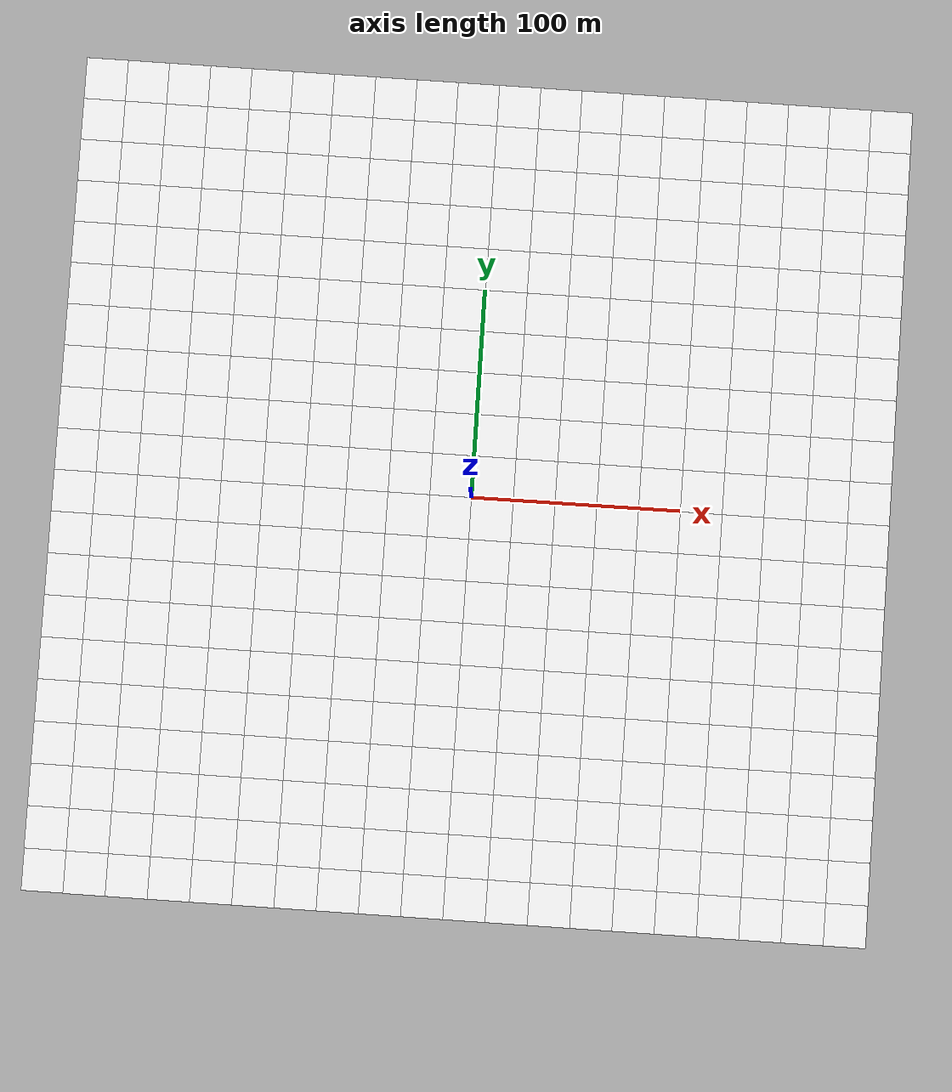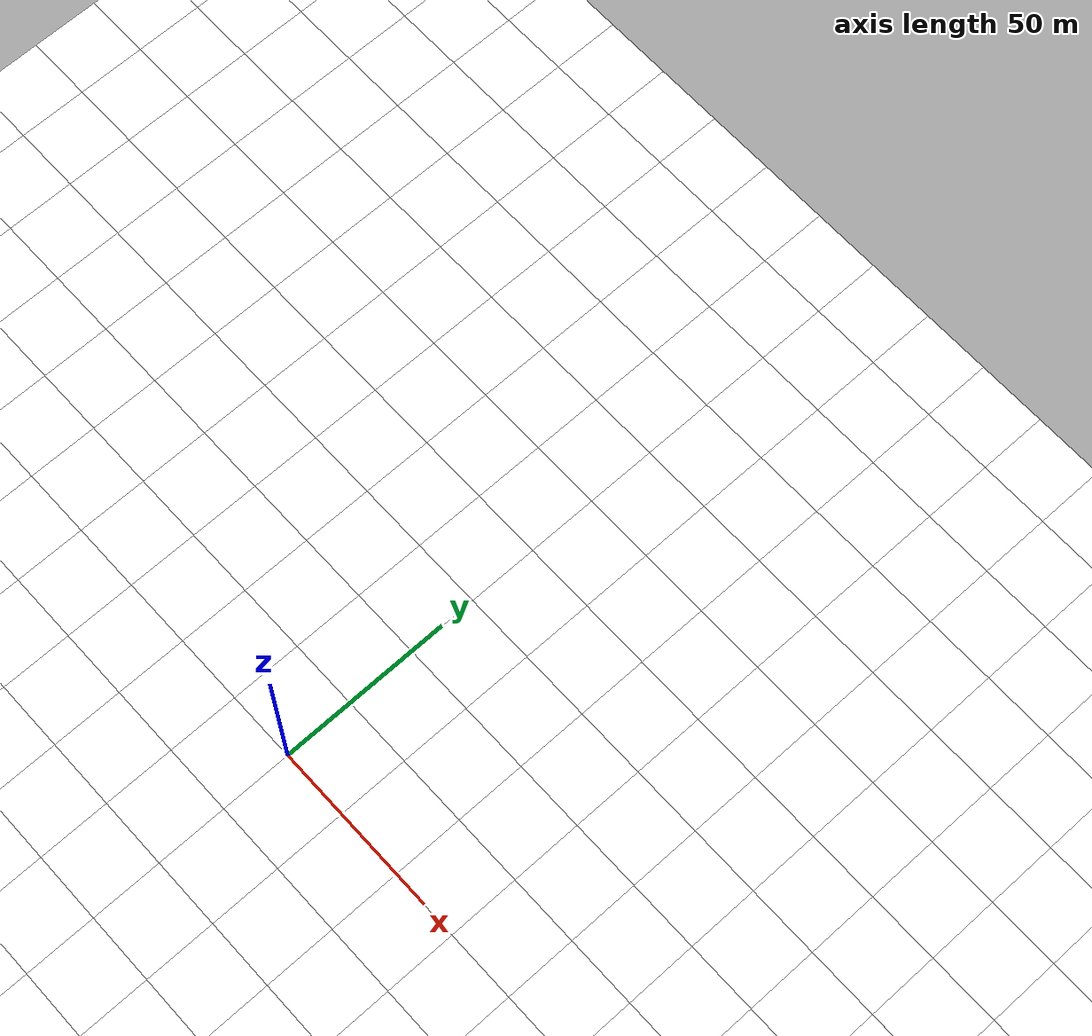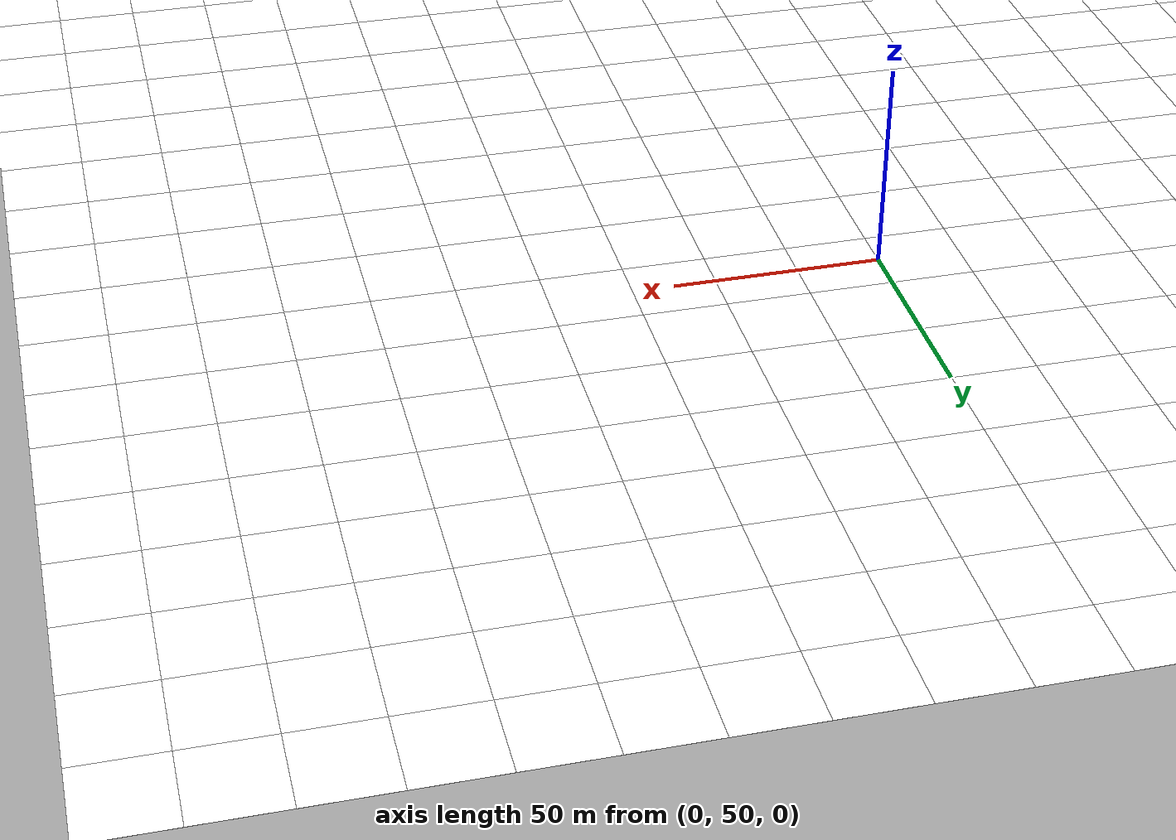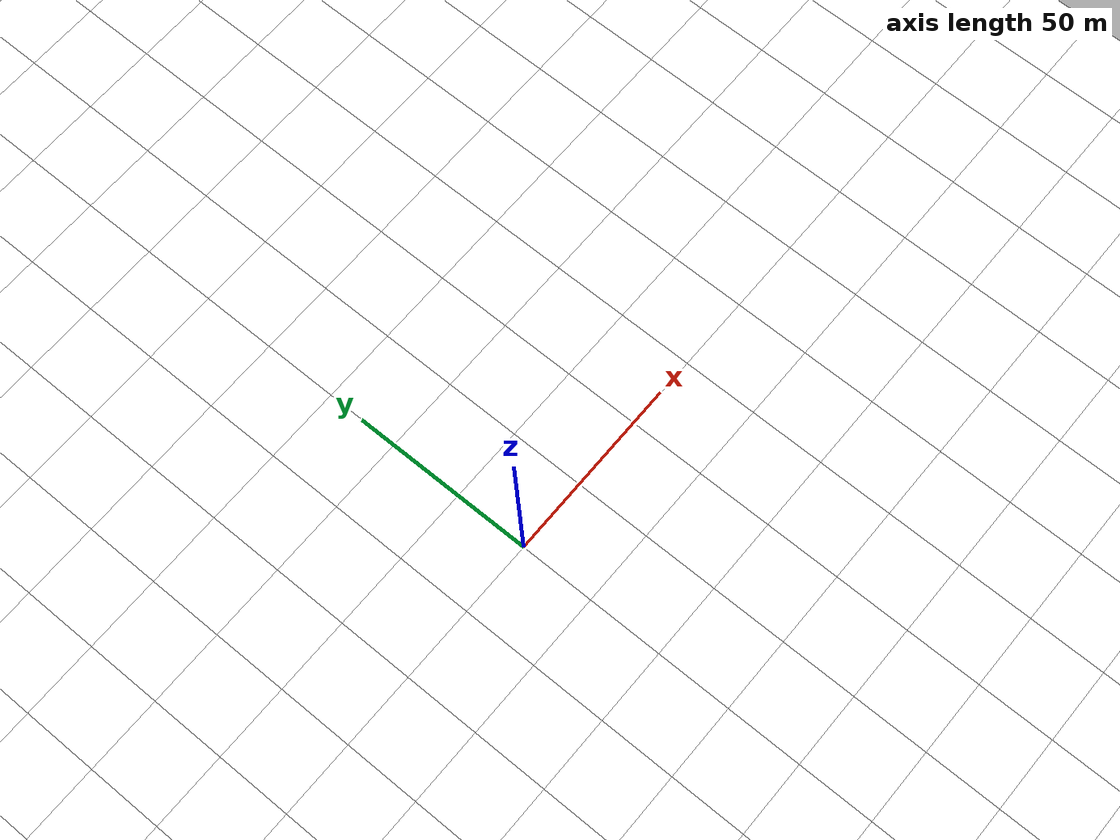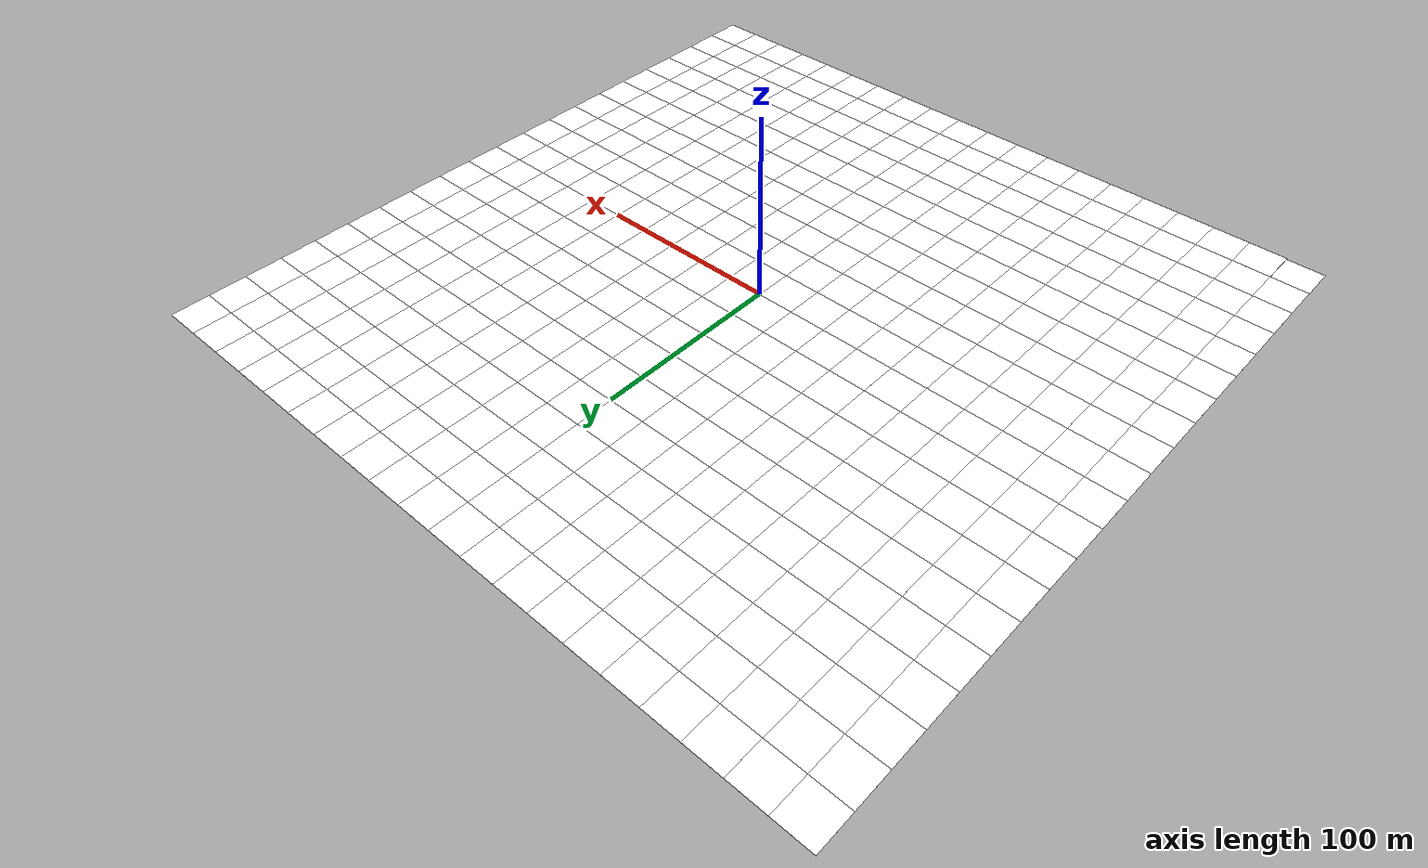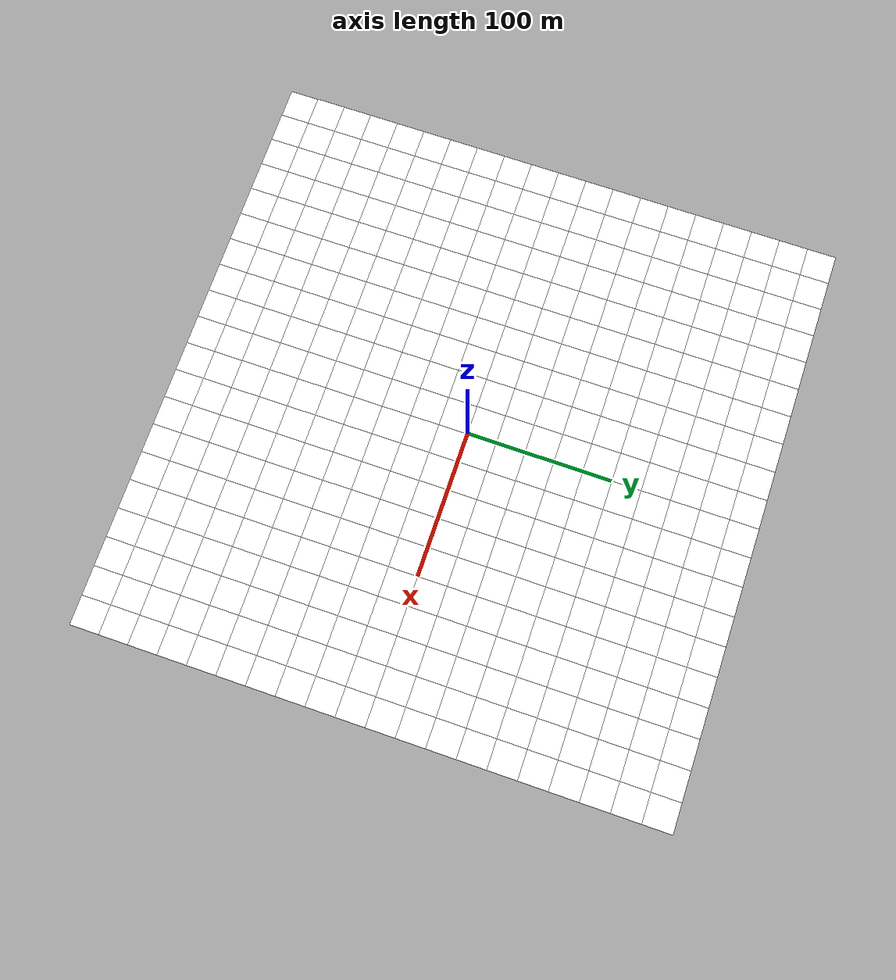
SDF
<?xml version="1.0" encoding="UTF-8"?>
<sdf version="1.9">
  <model name="grass_ground_big">
    <static>true</static>
    <link name="link">
      <collision name="collision">
        <geometry>
          <plane>
            <normal>0 0 1</normal>
            <size>400 400</size>
          </plane>
        </geometry>
      </collision>
      <!-- Siatka kafli 20x20 m -->
      <visual name="tile_0_0"><pose>-190 -190 0 0 0 0</pose><cast_shadows>false</cast_shadows><geometry><plane><normal>0 0 1</normal><size>20 20</size></plane></geometry><material><diffuse>1 1 1 1</diffuse><ambient>1 1 1 1</ambient><pbr><metal><albedo_map>materials/textures/grass_dry.png</albedo_map></metal></pbr></material></visual>
      <visual name="tile_1_0"><pose>-170 -190 0 0 0 0</pose><cast_shadows>false</cast_shadows><geometry><plane><normal>0 0 1</normal><size>20 20</size></plane></geometry><material><diffuse>1 1 1 1</diffuse><ambient>1 1 1 1</ambient><pbr><metal><albedo_map>materials/textures/grass_dry.png</albedo_map></metal></pbr></material></visual>
      <visual name="tile_2_0"><pose>-150 -190 0 0 0 0</pose><cast_shadows>false</cast_shadows><geometry><plane><normal>0 0 1</normal><size>20 20</size></plane></geometry><material><diffuse>1 1 1 1</diffuse><ambient>1 1 1 1</ambient><pbr><metal><albedo_map>materials/textures/grass_dry.png</albedo_map></metal></pbr></material></visual>
      <visual name="tile_3_0"><pose>-130 -190 0 0 0 0</pose><cast_shadows>false</cast_shadows><geometry><plane><normal>0 0 1</normal><size>20 20</size></plane></geometry><material><diffuse>1 1 1 1</diffuse><ambient>1 1 1 1</ambient><pbr><metal><albedo_map>materials/textures/grass_dry.png</albedo_map></metal></pbr></material></visual>
      <visual name="tile_4_0"><pose>-110 -190 0 0 0 0</pose><cast_shadows>false</cast_shadows><geometry><plane><normal>0 0 1</normal><size>20 20</size></plane></geometry><material><diffuse>1 1 1 1</diffuse><ambient>1 1 1 1</ambient><pbr><metal><albedo_map>materials/textures/grass_dry.png</albedo_map></metal></pbr></material></visual>
      <visual name="tile_5_0"><pose>-90 -190 0 0 0 0</pose><cast_shadows>false</cast_shadows><geometry><plane><normal>0 0 1</normal><size>20 20</size></plane></geometry><material><diffuse>1 1 1 1</diffuse><ambient>1 1 1 1</ambient><pbr><metal><albedo_map>materials/textures/grass_dry.png</albedo_map></metal></pbr></material></visual>
      <visual name="tile_6_0"><pose>-70 -190 0 0 0 0</pose><cast_shadows>false</cast_shadows><geometry><plane><normal>0 0 1</normal><size>20 20</size></plane></geometry><material><diffuse>1 1 1 1</diffuse><ambient>1 1 1 1</ambient><pbr><metal><albedo_map>materials/textures/grass_dry.png</albedo_map></metal></pbr></material></visual>
      <visual name="tile_7_0"><pose>-50 -190 0 0 0 0</pose><cast_shadows>false</cast_shadows><geometry><plane><normal>0 0 1</normal><size>20 20</size></plane></geometry><material><diffuse>1 1 1 1</diffuse><ambient>1 1 1 1</ambient><pbr><metal><albedo_map>materials/textures/grass_dry.png</albedo_map></metal></pbr></material></visual>
      <visual name="tile_8_0"><pose>-30 -190 0 0 0 0</pose><cast_shadows>false</cast_shadows><geometry><plane><normal>0 0 1</normal><size>20 20</size></plane></geometry><material><diffuse>1 1 1 1</diffuse><ambient>1 1 1 1</ambient><pbr><metal><albedo_map>materials/textures/grass_dry.png</albedo_map></metal></pbr></material></visual>
      <visual name="tile_9_0"><pose>-10 -190 0 0 0 0</pose><cast_shadows>false</cast_shadows><geometry><plane><normal>0 0 1</normal><size>20 20</size></plane></geometry><material><diffuse>1 1 1 1</diffuse><ambient>1 1 1 1</ambient><pbr><metal><albedo_map>materials/textures/grass_dry.png</albedo_map></metal></pbr></material></visual>
      <visual name="tile_10_0"><pose>10 -190 0 0 0 0</pose><cast_shadows>false</cast_shadows><geometry><plane><normal>0 0 1</normal><size>20 20</size></plane></geometry><material><diffuse>1 1 1 1</diffuse><ambient>1 1 1 1</ambient><pbr><metal><albedo_map>materials/textures/grass_dry.png</albedo_map></metal></pbr></material></visual>
      <visual name="tile_11_0"><pose>30 -190 0 0 0 0</pose><cast_shadows>false</cast_shadows><geometry><plane><normal>0 0 1</normal><size>20 20</size></plane></geometry><material><diffuse>1 1 1 1</diffuse><ambient>1 1 1 1</ambient><pbr><metal><albedo_map>materials/textures/grass_dry.png</albedo_map></metal></pbr></material></visual>
      <visual name="tile_12_0"><pose>50 -190 0 0 0 0</pose><cast_shadows>false</cast_shadows><geometry><plane><normal>0 0 1</normal><size>20 20</size></plane></geometry><material><diffuse>1 1 1 1</diffuse><ambient>1 1 1 1</ambient><pbr><metal><albedo_map>materials/textures/grass_dry.png</albedo_map></metal></pbr></material></visual>
      <visual name="tile_13_0"><pose>70 -190 0 0 0 0</pose><cast_shadows>false</cast_shadows><geometry><plane><normal>0 0 1</normal><size>20 20</size></plane></geometry><material><diffuse>1 1 1 1</diffuse><ambient>1 1 1 1</ambient><pbr><metal><albedo_map>materials/textures/grass_dry.png</albedo_map></metal></pbr></material></visual>
      <visual name="tile_14_0"><pose>90 -190 0 0 0 0</pose><cast_shadows>false</cast_shadows><geometry><plane><normal>0 0 1</normal><size>20 20</size></plane></geometry><material><diffuse>1 1 1 1</diffuse><ambient>1 1 1 1</ambient><pbr><metal><albedo_map>materials/textures/grass_dry.png</albedo_map></metal></pbr></material></visual>
      <visual name="tile_15_0"><pose>110 -190 0 0 0 0</pose><cast_shadows>false</cast_shadows><geometry><plane><normal>0 0 1</normal><size>20 20</size></plane></geometry><material><diffuse>1 1 1 1</diffuse><ambient>1 1 1 1</ambient><pbr><metal><albedo_map>materials/textures/grass_dry.png</albedo_map></metal></pbr></material></visual>
      <visual name="tile_16_0"><pose>130 -190 0 0 0 0</pose><cast_shadows>false</cast_shadows><geometry><plane><normal>0 0 1</normal><size>20 20</size></plane></geometry><material><diffuse>1 1 1 1</diffuse><ambient>1 1 1 1</ambient><pbr><metal><albedo_map>materials/textures/grass_dry.png</albedo_map></metal></pbr></material></visual>
      <visual name="tile_17_0"><pose>150 -190 0 0 0 0</pose><cast_shadows>false</cast_shadows><geometry><plane><normal>0 0 1</normal><size>20 20</size></plane></geometry><material><diffuse>1 1 1 1</diffuse><ambient>1 1 1 1</ambient><pbr><metal><albedo_map>materials/textures/grass_dry.png</albedo_map></metal></pbr></material></visual>
      <visual name="tile_18_0"><pose>170 -190 0 0 0 0</pose><cast_shadows>false</cast_shadows><geometry><plane><normal>0 0 1</normal><size>20 20</size></plane></geometry><material><diffuse>1 1 1 1</diffuse><ambient>1 1 1 1</ambient><pbr><metal><albedo_map>materials/textures/grass_dry.png</albedo_map></metal></pbr></material></visual>
      <visual name="tile_19_0"><pose>190 -190 0 0 0 0</pose><cast_shadows>false</cast_shadows><geometry><plane><normal>0 0 1</normal><size>20 20</size></plane></geometry><material><diffuse>1 1 1 1</diffuse><ambient>1 1 1 1</ambient><pbr><metal><albedo_map>materials/textures/grass_dry.png</albedo_map></metal></pbr></material></visual>
      <visual name="tile_0_1"><pose>-190 -170 0 0 0 0</pose><cast_shadows>false</cast_shadows><geometry><plane><normal>0 0 1</normal><size>20 20</size></plane></geometry><material><diffuse>1 1 1 1</diffuse><ambient>1 1 1 1</ambient><pbr><metal><albedo_map>materials/textures/grass_dry.png</albedo_map></metal></pbr></material></visual>
      <visual name="tile_1_1"><pose>-170 -170 0 0 0 0</pose><cast_shadows>false</cast_shadows><geometry><plane><normal>0 0 1</normal><size>20 20</size></plane></geometry><material><diffuse>1 1 1 1</diffuse><ambient>1 1 1 1</ambient><pbr><metal><albedo_map>materials/textures/grass_dry.png</albedo_map></metal></pbr></material></visual>
      <visual name="tile_2_1"><pose>-150 -170 0 0 0 0</pose><cast_shadows>false</cast_shadows><geometry><plane><normal>0 0 1</normal><size>20 20</size></plane></geometry><material><diffuse>1 1 1 1</diffuse><ambient>1 1 1 1</ambient><pbr><metal><albedo_map>materials/textures/grass_dry.png</albedo_map></metal></pbr></material></visual>
      <visual name="tile_3_1"><pose>-130 -170 0 0 0 0</pose><cast_shadows>false</cast_shadows><geometry><plane><normal>0 0 1</normal><size>20 20</size></plane></geometry><material><diffuse>1 1 1 1</diffuse><ambient>1 1 1 1</ambient><pbr><metal><albedo_map>materials/textures/grass_dry.png</albedo_map></metal></pbr></material></visual>
      <visual name="tile_4_1"><pose>-110 -170 0 0 0 0</pose><cast_shadows>false</cast_shadows><geometry><plane><normal>0 0 1</normal><size>20 20</size></plane></geometry><material><diffuse>1 1 1 1</diffuse><ambient>1 1 1 1</ambient><pbr><metal><albedo_map>materials/textures/grass_dry.png</albedo_map></metal></pbr></material></visual>
      <visual name="tile_5_1"><pose>-90 -170 0 0 0 0</pose><cast_shadows>false</cast_shadows><geometry><plane><normal>0 0 1</normal><size>20 20</size></plane></geometry><material><diffuse>1 1 1 1</diffuse><ambient>1 1 1 1</ambient><pbr><metal><albedo_map>materials/textures/grass_dry.png</albedo_map></metal></pbr></material></visual>
      <visual name="tile_6_1"><pose>-70 -170 0 0 0 0</pose><cast_shadows>false</cast_shadows><geometry><plane><normal>0 0 1</normal><size>20 20</size></plane></geometry><material><diffuse>1 1 1 1</diffuse><ambient>1 1 1 1</ambient><pbr><metal><albedo_map>materials/textures/grass_dry.png</albedo_map></metal></pbr></material></visual>
      <visual name="tile_7_1"><pose>-50 -170 0 0 0 0</pose><cast_shadows>false</cast_shadows><geometry><plane><normal>0 0 1</normal><size>20 20</size></plane></geometry><material><diffuse>1 1 1 1</diffuse><ambient>1 1 1 1</ambient><pbr><metal><albedo_map>materials/textures/grass_dry.png</albedo_map></metal></pbr></material></visual>
      <visual name="tile_8_1"><pose>-30 -170 0 0 0 0</pose><cast_shadows>false</cast_shadows><geometry><plane><normal>0 0 1</normal><size>20 20</size></plane></geometry><material><diffuse>1 1 1 1</diffuse><ambient>1 1 1 1</ambient><pbr><metal><albedo_map>materials/textures/grass_dry.png</albedo_map></metal></pbr></material></visual>
      <visual name="tile_9_1"><pose>-10 -170 0 0 0 0</pose><cast_shadows>false</cast_shadows><geometry><plane><normal>0 0 1</normal><size>20 20</size></plane></geometry><material><diffuse>1 1 1 1</diffuse><ambient>1 1 1 1</ambient><pbr><metal><albedo_map>materials/textures/grass_dry.png</albedo_map></metal></pbr></material></visual>
      <visual name="tile_10_1"><pose>10 -170 0 0 0 0</pose><cast_shadows>false</cast_shadows><geometry><plane><normal>0 0 1</normal><size>20 20</size></plane></geometry><material><diffuse>1 1 1 1</diffuse><ambient>1 1 1 1</ambient><pbr><metal><albedo_map>materials/textures/grass_dry.png</albedo_map></metal></pbr></material></visual>
      <visual name="tile_11_1"><pose>30 -170 0 0 0 0</pose><cast_shadows>false</cast_shadows><geometry><plane><normal>0 0 1</normal><size>20 20</size></plane></geometry><material><diffuse>1 1 1 1</diffuse><ambient>1 1 1 1</ambient><pbr><metal><albedo_map>materials/textures/grass_dry.png</albedo_map></metal></pbr></material></visual>
      <visual name="tile_12_1"><pose>50 -170 0 0 0 0</pose><cast_shadows>false</cast_shadows><geometry><plane><normal>0 0 1</normal><size>20 20</size></plane></geometry><material><diffuse>1 1 1 1</diffuse><ambient>1 1 1 1</ambient><pbr><metal><albedo_map>materials/textures/grass_dry.png</albedo_map></metal></pbr></material></visual>
      <visual name="tile_13_1"><pose>70 -170 0 0 0 0</pose><cast_shadows>false</cast_shadows><geometry><plane><normal>0 0 1</normal><size>20 20</size></plane></geometry><material><diffuse>1 1 1 1</diffuse><ambient>1 1 1 1</ambient><pbr><metal><albedo_map>materials/textures/grass_dry.png</albedo_map></metal></pbr></material></visual>
      <visual name="tile_14_1"><pose>90 -170 0 0 0 0</pose><cast_shadows>false</cast_shadows><geometry><plane><normal>0 0 1</normal><size>20 20</size></plane></geometry><material><diffuse>1 1 1 1</diffuse><ambient>1 1 1 1</ambient><pbr><metal><albedo_map>materials/textures/grass_dry.png</albedo_map></metal></pbr></material></visual>
      <visual name="tile_15_1"><pose>110 -170 0 0 0 0</pose><cast_shadows>false</cast_shadows><geometry><plane><normal>0 0 1</normal><size>20 20</size></plane></geometry><material><diffuse>1 1 1 1</diffuse><ambient>1 1 1 1</ambient><pbr><metal><albedo_map>materials/textures/grass_dry.png</albedo_map></metal></pbr></material></visual>
      <visual name="tile_16_1"><pose>130 -170 0 0 0 0</pose><cast_shadows>false</cast_shadows><geometry><plane><normal>0 0 1</normal><size>20 20</size></plane></geometry><material><diffuse>1 1 1 1</diffuse><ambient>1 1 1 1</ambient><pbr><metal><albedo_map>materials/textures/grass_dry.png</albedo_map></metal></pbr></material></visual>
      <visual name="tile_17_1"><pose>150 -170 0 0 0 0</pose><cast_shadows>false</cast_shadows><geometry><plane><normal>0 0 1</normal><size>20 20</size></plane></geometry><material><diffuse>1 1 1 1</diffuse><ambient>1 1 1 1</ambient><pbr><metal><albedo_map>materials/textures/grass_dry.png</albedo_map></metal></pbr></material></visual>
      <visual name="tile_18_1"><pose>170 -170 0 0 0 0</pose><cast_shadows>false</cast_shadows><geometry><plane><normal>0 0 1</normal><size>20 20</size></plane></geometry><material><diffuse>1 1 1 1</diffuse><ambient>1 1 1 1</ambient><pbr><metal><albedo_map>materials/textures/grass_dry.png</albedo_map></metal></pbr></material></visual>
      <visual name="tile_19_1"><pose>190 -170 0 0 0 0</pose><cast_shadows>false</cast_shadows><geometry><plane><normal>0 0 1</normal><size>20 20</size></plane></geometry><material><diffuse>1 1 1 1</diffuse><ambient>1 1 1 1</ambient><pbr><metal><albedo_map>materials/textures/grass_dry.png</albedo_map></metal></pbr></material></visual>
      <visual name="tile_0_2"><pose>-190 -150 0 0 0 0</pose><cast_shadows>false</cast_shadows><geometry><plane><normal>0 0 1</normal><size>20 20</size></plane></geometry><material><diffuse>1 1 1 1</diffuse><ambient>1 1 1 1</ambient><pbr><metal><albedo_map>materials/textures/grass_dry.png</albedo_map></metal></pbr></material></visual>
      <visual name="tile_1_2"><pose>-170 -150 0 0 0 0</pose><cast_shadows>false</cast_shadows><geometry><plane><normal>0 0 1</normal><size>20 20</size></plane></geometry><material><diffuse>1 1 1 1</diffuse><ambient>1 1 1 1</ambient><pbr><metal><albedo_map>materials/textures/grass_dry.png</albedo_map></metal></pbr></material></visual>
      <visual name="tile_2_2"><pose>-150 -150 0 0 0 0</pose><cast_shadows>false</cast_shadows><geometry><plane><normal>0 0 1</normal><size>20 20</size></plane></geometry><material><diffuse>1 1 1 1</diffuse><ambient>1 1 1 1</ambient><pbr><metal><albedo_map>materials/textures/grass_dry.png</albedo_map></metal></pbr></material></visual>
      <visual name="tile_3_2"><pose>-130 -150 0 0 0 0</pose><cast_shadows>false</cast_shadows><geometry><plane><normal>0 0 1</normal><size>20 20</size></plane></geometry><material><diffuse>1 1 1 1</diffuse><ambient>1 1 1 1</ambient><pbr><metal><albedo_map>materials/textures/grass_dry.png</albedo_map></metal></pbr></material></visual>
      <visual name="tile_4_2"><pose>-110 -150 0 0 0 0</pose><cast_shadows>false</cast_shadows><geometry><plane><normal>0 0 1</normal><size>20 20</size></plane></geometry><material><diffuse>1 1 1 1</diffuse><ambient>1 1 1 1</ambient><pbr><metal><albedo_map>materials/textures/grass_dry.png</albedo_map></metal></pbr></material></visual>
      <visual name="tile_5_2"><pose>-90 -150 0 0 0 0</pose><cast_shadows>false</cast_shadows><geometry><plane><normal>0 0 1</normal><size>20 20</size></plane></geometry><material><diffuse>1 1 1 1</diffuse><ambient>1 1 1 1</ambient><pbr><metal><albedo_map>materials/textures/grass_dry.png</albedo_map></metal></pbr></material></visual>
      <visual name="tile_6_2"><pose>-70 -150 0 0 0 0</pose><cast_shadows>false</cast_shadows><geometry><plane><normal>0 0 1</normal><size>20 20</size></plane></geometry><material><diffuse>1 1 1 1</diffuse><ambient>1 1 1 1</ambient><pbr><metal><albedo_map>materials/textures/grass_dry.png</albedo_map></metal></pbr></material></visual>
      <visual name="tile_7_2"><pose>-50 -150 0 0 0 0</pose><cast_shadows>false</cast_shadows><geometry><plane><normal>0 0 1</normal><size>20 20</size></plane></geometry><material><diffuse>1 1 1 1</diffuse><ambient>1 1 1 1</ambient><pbr><metal><albedo_map>materials/textures/grass_dry.png</albedo_map></metal></pbr></material></visual>
      <visual name="tile_8_2"><pose>-30 -150 0 0 0 0</pose><cast_shadows>false</cast_shadows><geometry><plane><normal>0 0 1</normal><size>20 20</size></plane></geometry><material><diffuse>1 1 1 1</diffuse><ambient>1 1 1 1</ambient><pbr><metal><albedo_map>materials/textures/grass_dry.png</albedo_map></metal></pbr></material></visual>
      <visual name="tile_9_2"><pose>-10 -150 0 0 0 0</pose><cast_shadows>false</cast_shadows><geometry><plane><normal>0 0 1</normal><size>20 20</size></plane></geometry><material><diffuse>1 1 1 1</diffuse><ambient>1 1 1 1</ambient><pbr><metal><albedo_map>materials/textures/grass_dry.png</albedo_map></metal></pbr></material></visual>
      <visual name="tile_10_2"><pose>10 -150 0 0 0 0</pose><cast_shadows>false</cast_shadows><geometry><plane><normal>0 0 1</normal><size>20 20</size></plane></geometry><material><diffuse>1 1 1 1</diffuse><ambient>1 1 1 1</ambient><pbr><metal><albedo_map>materials/textures/grass_dry.png</albedo_map></metal></pbr></material></visual>
      <visual name="tile_11_2"><pose>30 -150 0 0 0 0</pose><cast_shadows>false</cast_shadows><geometry><plane><normal>0 0 1</normal><size>20 20</size></plane></geometry><material><diffuse>1 1 1 1</diffuse><ambient>1 1 1 1</ambient><pbr><metal><albedo_map>materials/textures/grass_dry.png</albedo_map></metal></pbr></material></visual>
      <visual name="tile_12_2"><pose>50 -150 0 0 0 0</pose><cast_shadows>false</cast_shadows><geometry><plane><normal>0 0 1</normal><size>20 20</size></plane></geometry><material><diffuse>1 1 1 1</diffuse><ambient>1 1 1 1</ambient><pbr><metal><albedo_map>materials/textures/grass_dry.png</albedo_map></metal></pbr></material></visual>
      <visual name="tile_13_2"><pose>70 -150 0 0 0 0</pose><cast_shadows>false</cast_shadows><geometry><plane><normal>0 0 1</normal><size>20 20</size></plane></geometry><material><diffuse>1 1 1 1</diffuse><ambient>1 1 1 1</ambient><pbr><metal><albedo_map>materials/textures/grass_dry.png</albedo_map></metal></pbr></material></visual>
      <visual name="tile_14_2"><pose>90 -150 0 0 0 0</pose><cast_shadows>false</cast_shadows><geometry><plane><normal>0 0 1</normal><size>20 20</size></plane></geometry><material><diffuse>1 1 1 1</diffuse><ambient>1 1 1 1</ambient><pbr><metal><albedo_map>materials/textures/grass_dry.png</albedo_map></metal></pbr></material></visual>
      <visual name="tile_15_2"><pose>110 -150 0 0 0 0</pose><cast_shadows>false</cast_shadows><geometry><plane><normal>0 0 1</normal><size>20 20</size></plane></geometry><material><diffuse>1 1 1 1</diffuse><ambient>1 1 1 1</ambient><pbr><metal><albedo_map>materials/textures/grass_dry.png</albedo_map></metal></pbr></material></visual>
      <visual name="tile_16_2"><pose>130 -150 0 0 0 0</pose><cast_shadows>false</cast_shadows><geometry><plane><normal>0 0 1</normal><size>20 20</size></plane></geometry><material><diffuse>1 1 1 1</diffuse><ambient>1 1 1 1</ambient><pbr><metal><albedo_map>materials/textures/grass_dry.png</albedo_map></metal></pbr></material></visual>
      <visual name="tile_17_2"><pose>150 -150 0 0 0 0</pose><cast_shadows>false</cast_shadows><geometry><plane><normal>0 0 1</normal><size>20 20</size></plane></geometry><material><diffuse>1 1 1 1</diffuse><ambient>1 1 1 1</ambient><pbr><metal><albedo_map>materials/textures/grass_dry.png</albedo_map></metal></pbr></material></visual>
      <visual name="tile_18_2"><pose>170 -150 0 0 0 0</pose><cast_shadows>false</cast_shadows><geometry><plane><normal>0 0 1</normal><size>20 20</size></plane></geometry><material><diffuse>1 1 1 1</diffuse><ambient>1 1 1 1</ambient><pbr><metal><albedo_map>materials/textures/grass_dry.png</albedo_map></metal></pbr></material></visual>
      <visual name="tile_19_2"><pose>190 -150 0 0 0 0</pose><cast_shadows>false</cast_shadows><geometry><plane><normal>0 0 1</normal><size>20 20</size></plane></geometry><material><diffuse>1 1 1 1</diffuse><ambient>1 1 1 1</ambient><pbr><metal><albedo_map>materials/textures/grass_dry.png</albedo_map></metal></pbr></material></visual>
      <visual name="tile_0_3"><pose>-190 -130 0 0 0 0</pose><cast_shadows>false</cast_shadows><geometry><plane><normal>0 0 1</normal><size>20 20</size></plane></geometry><material><diffuse>1 1 1 1</diffuse><ambient>1 1 1 1</ambient><pbr><metal><albedo_map>materials/textures/grass_dry.png</albedo_map></metal></pbr></material></visual>
      <visual name="tile_1_3"><pose>-170 -130 0 0 0 0</pose><cast_shadows>false</cast_shadows><geometry><plane><normal>0 0 1</normal><size>20 20</size></plane></geometry><material><diffuse>1 1 1 1</diffuse><ambient>1 1 1 1</ambient><pbr><metal><albedo_map>materials/textures/grass_dry.png</albedo_map></metal></pbr></material></visual>
      <visual name="tile_2_3"><pose>-150 -130 0 0 0 0</pose><cast_shadows>false</cast_shadows><geometry><plane><normal>0 0 1</normal><size>20 20</size></plane></geometry><material><diffuse>1 1 1 1</diffuse><ambient>1 1 1 1</ambient><pbr><metal><albedo_map>materials/textures/grass_dry.png</albedo_map></metal></pbr></material></visual>
      <visual name="tile_3_3"><pose>-130 -130 0 0 0 0</pose><cast_shadows>false</cast_shadows><geometry><plane><normal>0 0 1</normal><size>20 20</size></plane></geometry><material><diffuse>1 1 1 1</diffuse><ambient>1 1 1 1</ambient><pbr><metal><albedo_map>materials/textures/grass_dry.png</albedo_map></metal></pbr></material></visual>
      <visual name="tile_4_3"><pose>-110 -130 0 0 0 0</pose><cast_shadows>false</cast_shadows><geometry><plane><normal>0 0 1</normal><size>20 20</size></plane></geometry><material><diffuse>1 1 1 1</diffuse><ambient>1 1 1 1</ambient><pbr><metal><albedo_map>materials/textures/grass_dry.png</albedo_map></metal></pbr></material></visual>
      <visual name="tile_5_3"><pose>-90 -130 0 0 0 0</pose><cast_shadows>false</cast_shadows><geometry><plane><normal>0 0 1</normal><size>20 20</size></plane></geometry><material><diffuse>1 1 1 1</diffuse><ambient>1 1 1 1</ambient><pbr><metal><albedo_map>materials/textures/grass_dry.png</albedo_map></metal></pbr></material></visual>
      <visual name="tile_6_3"><pose>-70 -130 0 0 0 0</pose><cast_shadows>false</cast_shadows><geometry><plane><normal>0 0 1</normal><size>20 20</size></plane></geometry><material><diffuse>1 1 1 1</diffuse><ambient>1 1 1 1</ambient><pbr><metal><albedo_map>materials/textures/grass_dry.png</albedo_map></metal></pbr></material></visual>
      <visual name="tile_7_3"><pose>-50 -130 0 0 0 0</pose><cast_shadows>false</cast_shadows><geometry><plane><normal>0 0 1</normal><size>20 20</size></plane></geometry><material><diffuse>1 1 1 1</diffuse><ambient>1 1 1 1</ambient><pbr><metal><albedo_map>materials/textures/grass_dry.png</albedo_map></metal></pbr></material></visual>
      <visual name="tile_8_3"><pose>-30 -130 0 0 0 0</pose><cast_shadows>false</cast_shadows><geometry><plane><normal>0 0 1</normal><size>20 20</size></plane></geometry><material><diffuse>1 1 1 1</diffuse><ambient>1 1 1 1</ambient><pbr><metal><albedo_map>materials/textures/grass_dry.png</albedo_map></metal></pbr></material></visual>
      <visual name="tile_9_3"><pose>-10 -130 0 0 0 0</pose><cast_shadows>false</cast_shadows><geometry><plane><normal>0 0 1</normal><size>20 20</size></plane></geometry><material><diffuse>1 1 1 1</diffuse><ambient>1 1 1 1</ambient><pbr><metal><albedo_map>materials/textures/grass_dry.png</albedo_map></metal></pbr></material></visual>
      <visual name="tile_10_3"><pose>10 -130 0 0 0 0</pose><cast_shadows>false</cast_shadows><geometry><plane><normal>0 0 1</normal><size>20 20</size></plane></geometry><material><diffuse>1 1 1 1</diffuse><ambient>1 1 1 1</ambient><pbr><metal><albedo_map>materials/textures/grass_dry.png</albedo_map></metal></pbr></material></visual>
      <visual name="tile_11_3"><pose>30 -130 0 0 0 0</pose><cast_shadows>false</cast_shadows><geometry><plane><normal>0 0 1</normal><size>20 20</size></plane></geometry><material><diffuse>1 1 1 1</diffuse><ambient>1 1 1 1</ambient><pbr><metal><albedo_map>materials/textures/grass_dry.png</albedo_map></metal></pbr></material></visual>
      <visual name="tile_12_3"><pose>50 -130 0 0 0 0</pose><cast_shadows>false</cast_shadows><geometry><plane><normal>0 0 1</normal><size>20 20</size></plane></geometry><material><diffuse>1 1 1 1</diffuse><ambient>1 1 1 1</ambient><pbr><metal><albedo_map>materials/textures/grass_dry.png</albedo_map></metal></pbr></material></visual>
      <visual name="tile_13_3"><pose>70 -130 0 0 0 0</pose><cast_shadows>false</cast_shadows><geometry><plane><normal>0 0 1</normal><size>20 20</size></plane></geometry><material><diffuse>1 1 1 1</diffuse><ambient>1 1 1 1</ambient><pbr><metal><albedo_map>materials/textures/grass_dry.png</albedo_map></metal></pbr></material></visual>
      <visual name="tile_14_3"><pose>90 -130 0 0 0 0</pose><cast_shadows>false</cast_shadows><geometry><plane><normal>0 0 1</normal><size>20 20</size></plane></geometry><material><diffuse>1 1 1 1</diffuse><ambient>1 1 1 1</ambient><pbr><metal><albedo_map>materials/textures/grass_dry.png</albedo_map></metal></pbr></material></visual>
      <visual name="tile_15_3"><pose>110 -130 0 0 0 0</pose><cast_shadows>false</cast_shadows><geometry><plane><normal>0 0 1</normal><size>20 20</size></plane></geometry><material><diffuse>1 1 1 1</diffuse><ambient>1 1 1 1</ambient><pbr><metal><albedo_map>materials/textures/grass_dry.png</albedo_map></metal></pbr></material></visual>
      <visual name="tile_16_3"><pose>130 -130 0 0 0 0</pose><cast_shadows>false</cast_shadows><geometry><plane><normal>0 0 1</normal><size>20 20</size></plane></geometry><material><diffuse>1 1 1 1</diffuse><ambient>1 1 1 1</ambient><pbr><metal><albedo_map>materials/textures/grass_dry.png</albedo_map></metal></pbr></material></visual>
      <visual name="tile_17_3"><pose>150 -130 0 0 0 0</pose><cast_shadows>false</cast_shadows><geometry><plane><normal>0 0 1</normal><size>20 20</size></plane></geometry><material><diffuse>1 1 1 1</diffuse><ambient>1 1 1 1</ambient><pbr><metal><albedo_map>materials/textures/grass_dry.png</albedo_map></metal></pbr></material></visual>
      <visual name="tile_18_3"><pose>170 -130 0 0 0 0</pose><cast_shadows>false</cast_shadows><geometry><plane><normal>0 0 1</normal><size>20 20</size></plane></geometry><material><diffuse>1 1 1 1</diffuse><ambient>1 1 1 1</ambient><pbr><metal><albedo_map>materials/textures/grass_dry.png</albedo_map></metal></pbr></material></visual>
      <visual name="tile_19_3"><pose>190 -130 0 0 0 0</pose><cast_shadows>false</cast_shadows><geometry><plane><normal>0 0 1</normal><size>20 20</size></plane></geometry><material><diffuse>1 1 1 1</diffuse><ambient>1 1 1 1</ambient><pbr><metal><albedo_map>materials/textures/grass_dry.png</albedo_map></metal></pbr></material></visual>
      <visual name="tile_0_4"><pose>-190 -110 0 0 0 0</pose><cast_shadows>false</cast_shadows><geometry><plane><normal>0 0 1</normal><size>20 20</size></plane></geometry><material><diffuse>1 1 1 1</diffuse><ambient>1 1 1 1</ambient><pbr><metal><albedo_map>materials/textures/grass_dry.png</albedo_map></metal></pbr></material></visual>
      <visual name="tile_1_4"><pose>-170 -110 0 0 0 0</pose><cast_shadows>false</cast_shadows><geometry><plane><normal>0 0 1</normal><size>20 20</size></plane></geometry><material><diffuse>1 1 1 1</diffuse><ambient>1 1 1 1</ambient><pbr><metal><albedo_map>materials/textures/grass_dry.png</albedo_map></metal></pbr></material></visual>
      <visual name="tile_2_4"><pose>-150 -110 0 0 0 0</pose><cast_shadows>false</cast_shadows><geometry><plane><normal>0 0 1</normal><size>20 20</size></plane></geometry><material><diffuse>1 1 1 1</diffuse><ambient>1 1 1 1</ambient><pbr><metal><albedo_map>materials/textures/grass_dry.png</albedo_map></metal></pbr></material></visual>
      <visual name="tile_3_4"><pose>-130 -110 0 0 0 0</pose><cast_shadows>false</cast_shadows><geometry><plane><normal>0 0 1</normal><size>20 20</size></plane></geometry><material><diffuse>1 1 1 1</diffuse><ambient>1 1 1 1</ambient><pbr><metal><albedo_map>materials/textures/grass_dry.png</albedo_map></metal></pbr></material></visual>
      <visual name="tile_4_4"><pose>-110 -110 0 0 0 0</pose><cast_shadows>false</cast_shadows><geometry><plane><normal>0 0 1</normal><size>20 20</size></plane></geometry><material><diffuse>1 1 1 1</diffuse><ambient>1 1 1 1</ambient><pbr><metal><albedo_map>materials/textures/grass_dry.png</albedo_map></metal></pbr></material></visual>
      <visual name="tile_5_4"><pose>-90 -110 0 0 0 0</pose><cast_shadows>false</cast_shadows><geometry><plane><normal>0 0 1</normal><size>20 20</size></plane></geometry><material><diffuse>1 1 1 1</diffuse><ambient>1 1 1 1</ambient><pbr><metal><albedo_map>materials/textures/grass_dry.png</albedo_map></metal></pbr></material></visual>
      <visual name="tile_6_4"><pose>-70 -110 0 0 0 0</pose><cast_shadows>false</cast_shadows><geometry><plane><normal>0 0 1</normal><size>20 20</size></plane></geometry><material><diffuse>1 1 1 1</diffuse><ambient>1 1 1 1</ambient><pbr><metal><albedo_map>materials/textures/grass_dry.png</albedo_map></metal></pbr></material></visual>
      <visual name="tile_7_4"><pose>-50 -110 0 0 0 0</pose><cast_shadows>false</cast_shadows><geometry><plane><normal>0 0 1</normal><size>20 20</size></plane></geometry><material><diffuse>1 1 1 1</diffuse><ambient>1 1 1 1</ambient><pbr><metal><albedo_map>materials/textures/grass_dry.png</albedo_map></metal></pbr></material></visual>
      <visual name="tile_8_4"><pose>-30 -110 0 0 0 0</pose><cast_shadows>false</cast_shadows><geometry><plane><normal>0 0 1</normal><size>20 20</size></plane></geometry><material><diffuse>1 1 1 1</diffuse><ambient>1 1 1 1</ambient><pbr><metal><albedo_map>materials/textures/grass_dry.png</albedo_map></metal></pbr></material></visual>
      <visual name="tile_9_4"><pose>-10 -110 0 0 0 0</pose><cast_shadows>false</cast_shadows><geometry><plane><normal>0 0 1</normal><size>20 20</size></plane></geometry><material><diffuse>1 1 1 1</diffuse><ambient>1 1 1 1</ambient><pbr><metal><albedo_map>materials/textures/grass_dry.png</albedo_map></metal></pbr></material></visual>
      <visual name="tile_10_4"><pose>10 -110 0 0 0 0</pose><cast_shadows>false</cast_shadows><geometry><plane><normal>0 0 1</normal><size>20 20</size></plane></geometry><material><diffuse>1 1 1 1</diffuse><ambient>1 1 1 1</ambient><pbr><metal><albedo_map>materials/textures/grass_dry.png</albedo_map></metal></pbr></material></visual>
      <visual name="tile_11_4"><pose>30 -110 0 0 0 0</pose><cast_shadows>false</cast_shadows><geometry><plane><normal>0 0 1</normal><size>20 20</size></plane></geometry><material><diffuse>1 1 1 1</diffuse><ambient>1 1 1 1</ambient><pbr><metal><albedo_map>materials/textures/grass_dry.png</albedo_map></metal></pbr></material></visual>
      <visual name="tile_12_4"><pose>50 -110 0 0 0 0</pose><cast_shadows>false</cast_shadows><geometry><plane><normal>0 0 1</normal><size>20 20</size></plane></geometry><material><diffuse>1 1 1 1</diffuse><ambient>1 1 1 1</ambient><pbr><metal><albedo_map>materials/textures/grass_dry.png</albedo_map></metal></pbr></material></visual>
      <visual name="tile_13_4"><pose>70 -110 0 0 0 0</pose><cast_shadows>false</cast_shadows><geometry><plane><normal>0 0 1</normal><size>20 20</size></plane></geometry><material><diffuse>1 1 1 1</diffuse><ambient>1 1 1 1</ambient><pbr><metal><albedo_map>materials/textures/grass_dry.png</albedo_map></metal></pbr></material></visual>
      <visual name="tile_14_4"><pose>90 -110 0 0 0 0</pose><cast_shadows>false</cast_shadows><geometry><plane><normal>0 0 1</normal><size>20 20</size></plane></geometry><material><diffuse>1 1 1 1</diffuse><ambient>1 1 1 1</ambient><pbr><metal><albedo_map>materials/textures/grass_dry.png</albedo_map></metal></pbr></material></visual>
      <visual name="tile_15_4"><pose>110 -110 0 0 0 0</pose><cast_shadows>false</cast_shadows><geometry><plane><normal>0 0 1</normal><size>20 20</size></plane></geometry><material><diffuse>1 1 1 1</diffuse><ambient>1 1 1 1</ambient><pbr><metal><albedo_map>materials/textures/grass_dry.png</albedo_map></metal></pbr></material></visual>
      <visual name="tile_16_4"><pose>130 -110 0 0 0 0</pose><cast_shadows>false</cast_shadows><geometry><plane><normal>0 0 1</normal><size>20 20</size></plane></geometry><material><diffuse>1 1 1 1</diffuse><ambient>1 1 1 1</ambient><pbr><metal><albedo_map>materials/textures/grass_dry.png</albedo_map></metal></pbr></material></visual>
      <visual name="tile_17_4"><pose>150 -110 0 0 0 0</pose><cast_shadows>false</cast_shadows><geometry><plane><normal>0 0 1</normal><size>20 20</size></plane></geometry><material><diffuse>1 1 1 1</diffuse><ambient>1 1 1 1</ambient><pbr><metal><albedo_map>materials/textures/grass_dry.png</albedo_map></metal></pbr></material></visual>
      <visual name="tile_18_4"><pose>170 -110 0 0 0 0</pose><cast_shadows>false</cast_shadows><geometry><plane><normal>0 0 1</normal><size>20 20</size></plane></geometry><material><diffuse>1 1 1 1</diffuse><ambient>1 1 1 1</ambient><pbr><metal><albedo_map>materials/textures/grass_dry.png</albedo_map></metal></pbr></material></visual>
      <visual name="tile_19_4"><pose>190 -110 0 0 0 0</pose><cast_shadows>false</cast_shadows><geometry><plane><normal>0 0 1</normal><size>20 20</size></plane></geometry><material><diffuse>1 1 1 1</diffuse><ambient>1 1 1 1</ambient><pbr><metal><albedo_map>materials/textures/grass_dry.png</albedo_map></metal></pbr></material></visual>
      <visual name="tile_0_5"><pose>-190 -90 0 0 0 0</pose><cast_shadows>false</cast_shadows><geometry><plane><normal>0 0 1</normal><size>20 20</size></plane></geometry><material><diffuse>1 1 1 1</diffuse><ambient>1 1 1 1</ambient><pbr><metal><albedo_map>materials/textures/grass_dry.png</albedo_map></metal></pbr></material></visual>
      <visual name="tile_1_5"><pose>-170 -90 0 0 0 0</pose><cast_shadows>false</cast_shadows><geometry><plane><normal>0 0 1</normal><size>20 20</size></plane></geometry><material><diffuse>1 1 1 1</diffuse><ambient>1 1 1 1</ambient><pbr><metal><albedo_map>materials/textures/grass_dry.png</albedo_map></metal></pbr></material></visual>
      <visual name="tile_2_5"><pose>-150 -90 0 0 0 0</pose><cast_shadows>false</cast_shadows><geometry><plane><normal>0 0 1</normal><size>20 20</size></plane></geometry><material><diffuse>1 1 1 1</diffuse><ambient>1 1 1 1</ambient><pbr><metal><albedo_map>materials/textures/grass_dry.png</albedo_map></metal></pbr></material></visual>
      <visual name="tile_3_5"><pose>-130 -90 0 0 0 0</pose><cast_shadows>false</cast_shadows><geometry><plane><normal>0 0 1</normal><size>20 20</size></plane></geometry><material><diffuse>1 1 1 1</diffuse><ambient>1 1 1 1</ambient><pbr><metal><albedo_map>materials/textures/grass_dry.png</albedo_map></metal></pbr></material></visual>
      <visual name="tile_4_5"><pose>-110 -90 0 0 0 0</pose><cast_shadows>false</cast_shadows><geometry><plane><normal>0 0 1</normal><size>20 20</size></plane></geometry><material><diffuse>1 1 1 1</diffuse><ambient>1 1 1 1</ambient><pbr><metal><albedo_map>materials/textures/grass_dry.png</albedo_map></metal></pbr></material></visual>
      <visual name="tile_5_5"><pose>-90 -90 0 0 0 0</pose><cast_shadows>false</cast_shadows><geometry><plane><normal>0 0 1</normal><size>20 20</size></plane></geometry><material><diffuse>1 1 1 1</diffuse><ambient>1 1 1 1</ambient><pbr><metal><albedo_map>materials/textures/grass_dry.png</albedo_map></metal></pbr></material></visual>
      <visual name="tile_6_5"><pose>-70 -90 0 0 0 0</pose><cast_shadows>false</cast_shadows><geometry><plane><normal>0 0 1</normal><size>20 20</size></plane></geometry><material><diffuse>1 1 1 1</diffuse><ambient>1 1 1 1</ambient><pbr><metal><albedo_map>materials/textures/grass_dry.png</albedo_map></metal></pbr></material></visual>
      <visual name="tile_7_5"><pose>-50 -90 0 0 0 0</pose><cast_shadows>false</cast_shadows><geometry><plane><normal>0 0 1</normal><size>20 20</size></plane></geometry><material><diffuse>1 1 1 1</diffuse><ambient>1 1 1 1</ambient><pbr><metal><albedo_map>materials/textures/grass_dry.png</albedo_map></metal></pbr></material></visual>
      <visual name="tile_8_5"><pose>-30 -90 0 0 0 0</pose><cast_shadows>false</cast_shadows><geometry><plane><normal>0 0 1</normal><size>20 20</size></plane></geometry><material><diffuse>1 1 1 1</diffuse><ambient>1 1 1 1</ambient><pbr><metal><albedo_map>materials/textures/grass_dry.png</albedo_map></metal></pbr></material></visual>
      <visual name="tile_9_5"><pose>-10 -90 0 0 0 0</pose><cast_shadows>false</cast_shadows><geometry><plane><normal>0 0 1</normal><size>20 20</size></plane></geometry><material><diffuse>1 1 1 1</diffuse><ambient>1 1 1 1</ambient><pbr><metal><albedo_map>materials/textures/grass_dry.png</albedo_map></metal></pbr></material></visual>
      <visual name="tile_10_5"><pose>10 -90 0 0 0 0</pose><cast_shadows>false</cast_shadows><geometry><plane><normal>0 0 1</normal><size>20 20</size></plane></geometry><material><diffuse>1 1 1 1</diffuse><ambient>1 1 1 1</ambient><pbr><metal><albedo_map>materials/textures/grass_dry.png</albedo_map></metal></pbr></material></visual>
      <visual name="tile_11_5"><pose>30 -90 0 0 0 0</pose><cast_shadows>false</cast_shadows><geometry><plane><normal>0 0 1</normal><size>20 20</size></plane></geometry><material><diffuse>1 1 1 1</diffuse><ambient>1 1 1 1</ambient><pbr><metal><albedo_map>materials/textures/grass_dry.png</albedo_map></metal></pbr></material></visual>
      <visual name="tile_12_5"><pose>50 -90 0 0 0 0</pose><cast_shadows>false</cast_shadows><geometry><plane><normal>0 0 1</normal><size>20 20</size></plane></geometry><material><diffuse>1 1 1 1</diffuse><ambient>1 1 1 1</ambient><pbr><metal><albedo_map>materials/textures/grass_dry.png</albedo_map></metal></pbr></material></visual>
      <visual name="tile_13_5"><pose>70 -90 0 0 0 0</pose><cast_shadows>false</cast_shadows><geometry><plane><normal>0 0 1</normal><size>20 20</size></plane></geometry><material><diffuse>1 1 1 1</diffuse><ambient>1 1 1 1</ambient><pbr><metal><albedo_map>materials/textures/grass_dry.png</albedo_map></metal></pbr></material></visual>
      <visual name="tile_14_5"><pose>90 -90 0 0 0 0</pose><cast_shadows>false</cast_shadows><geometry><plane><normal>0 0 1</normal><size>20 20</size></plane></geometry><material><diffuse>1 1 1 1</diffuse><ambient>1 1 1 1</ambient><pbr><metal><albedo_map>materials/textures/grass_dry.png</albedo_map></metal></pbr></material></visual>
      <visual name="tile_15_5"><pose>110 -90 0 0 0 0</pose><cast_shadows>false</cast_shadows><geometry><plane><normal>0 0 1</normal><size>20 20</size></plane></geometry><material><diffuse>1 1 1 1</diffuse><ambient>1 1 1 1</ambient><pbr><metal><albedo_map>materials/textures/grass_dry.png</albedo_map></metal></pbr></material></visual>
      <visual name="tile_16_5"><pose>130 -90 0 0 0 0</pose><cast_shadows>false</cast_shadows><geometry><plane><normal>0 0 1</normal><size>20 20</size></plane></geometry><material><diffuse>1 1 1 1</diffuse><ambient>1 1 1 1</ambient><pbr><metal><albedo_map>materials/textures/grass_dry.png</albedo_map></metal></pbr></material></visual>
      <visual name="tile_17_5"><pose>150 -90 0 0 0 0</pose><cast_shadows>false</cast_shadows><geometry><plane><normal>0 0 1</normal><size>20 20</size></plane></geometry><material><diffuse>1 1 1 1</diffuse><ambient>1 1 1 1</ambient><pbr><metal><albedo_map>materials/textures/grass_dry.png</albedo_map></metal></pbr></material></visual>
      <visual name="tile_18_5"><pose>170 -90 0 0 0 0</pose><cast_shadows>false</cast_shadows><geometry><plane><normal>0 0 1</normal><size>20 20</size></plane></geometry><material><diffuse>1 1 1 1</diffuse><ambient>1 1 1 1</ambient><pbr><metal><albedo_map>materials/textures/grass_dry.png</albedo_map></metal></pbr></material></visual>
      <visual name="tile_19_5"><pose>190 -90 0 0 0 0</pose><cast_shadows>false</cast_shadows><geometry><plane><normal>0 0 1</normal><size>20 20</size></plane></geometry><material><diffuse>1 1 1 1</diffuse><ambient>1 1 1 1</ambient><pbr><metal><albedo_map>materials/textures/grass_dry.png</albedo_map></metal></pbr></material></visual>
      <visual name="tile_0_6"><pose>-190 -70 0 0 0 0</pose><cast_shadows>false</cast_shadows><geometry><plane><normal>0 0 1</normal><size>20 20</size></plane></geometry><material><diffuse>1 1 1 1</diffuse><ambient>1 1 1 1</ambient><pbr><metal><albedo_map>materials/textures/grass_dry.png</albedo_map></metal></pbr></material></visual>
      <visual name="tile_1_6"><pose>-170 -70 0 0 0 0</pose><cast_shadows>false</cast_shadows><geometry><plane><normal>0 0 1</normal><size>20 20</size></plane></geometry><material><diffuse>1 1 1 1</diffuse><ambient>1 1 1 1</ambient><pbr><metal><albedo_map>materials/textures/grass_dry.png</albedo_map></metal></pbr></material></visual>
      <visual name="tile_2_6"><pose>-150 -70 0 0 0 0</pose><cast_shadows>false</cast_shadows><geometry><plane><normal>0 0 1</normal><size>20 20</size></plane></geometry><material><diffuse>1 1 1 1</diffuse><ambient>1 1 1 1</ambient><pbr><metal><albedo_map>materials/textures/grass_dry.png</albedo_map></metal></pbr></material></visual>
      <visual name="tile_3_6"><pose>-130 -70 0 0 0 0</pose><cast_shadows>false</cast_shadows><geometry><plane><normal>0 0 1</normal><size>20 20</size></plane></geometry><material><diffuse>1 1 1 1</diffuse><ambient>1 1 1 1</ambient><pbr><metal><albedo_map>materials/textures/grass_dry.png</albedo_map></metal></pbr></material></visual>
      <visual name="tile_4_6"><pose>-110 -70 0 0 0 0</pose><cast_shadows>false</cast_shadows><geometry><plane><normal>0 0 1</normal><size>20 20</size></plane></geometry><material><diffuse>1 1 1 1</diffuse><ambient>1 1 1 1</ambient><pbr><metal><albedo_map>materials/textures/grass_dry.png</albedo_map></metal></pbr></material></visual>
      <visual name="tile_5_6"><pose>-90 -70 0 0 0 0</pose><cast_shadows>false</cast_shadows><geometry><plane><normal>0 0 1</normal><size>20 20</size></plane></geometry><material><diffuse>1 1 1 1</diffuse><ambient>1 1 1 1</ambient><pbr><metal><albedo_map>materials/textures/grass_dry.png</albedo_map></metal></pbr></material></visual>
      <visual name="tile_6_6"><pose>-70 -70 0 0 0 0</pose><cast_shadows>false</cast_shadows><geometry><plane><normal>0 0 1</normal><size>20 20</size></plane></geometry><material><diffuse>1 1 1 1</diffuse><ambient>1 1 1 1</ambient><pbr><metal><albedo_map>materials/textures/grass_dry.png</albedo_map></metal></pbr></material></visual>
      <visual name="tile_7_6"><pose>-50 -70 0 0 0 0</pose><cast_shadows>false</cast_shadows><geometry><plane><normal>0 0 1</normal><size>20 20</size></plane></geometry><material><diffuse>1 1 1 1</diffuse><ambient>1 1 1 1</ambient><pbr><metal><albedo_map>materials/textures/grass_dry.png</albedo_map></metal></pbr></material></visual>
      <visual name="tile_8_6"><pose>-30 -70 0 0 0 0</pose><cast_shadows>false</cast_shadows><geometry><plane><normal>0 0 1</normal><size>20 20</size></plane></geometry><material><diffuse>1 1 1 1</diffuse><ambient>1 1 1 1</ambient><pbr><metal><albedo_map>materials/textures/grass_dry.png</albedo_map></metal></pbr></material></visual>
      <visual name="tile_9_6"><pose>-10 -70 0 0 0 0</pose><cast_shadows>false</cast_shadows><geometry><plane><normal>0 0 1</normal><size>20 20</size></plane></geometry><material><diffuse>1 1 1 1</diffuse><ambient>1 1 1 1</ambient><pbr><metal><albedo_map>materials/textures/grass_dry.png</albedo_map></metal></pbr></material></visual>
      <visual name="tile_10_6"><pose>10 -70 0 0 0 0</pose><cast_shadows>false</cast_shadows><geometry><plane><normal>0 0 1</normal><size>20 20</size></plane></geometry><material><diffuse>1 1 1 1</diffuse><ambient>1 1 1 1</ambient><pbr><metal><albedo_map>materials/textures/grass_dry.png</albedo_map></metal></pbr></material></visual>
      <visual name="tile_11_6"><pose>30 -70 0 0 0 0</pose><cast_shadows>false</cast_shadows><geometry><plane><normal>0 0 1</normal><size>20 20</size></plane></geometry><material><diffuse>1 1 1 1</diffuse><ambient>1 1 1 1</ambient><pbr><metal><albedo_map>materials/textures/grass_dry.png</albedo_map></metal></pbr></material></visual>
      <visual name="tile_12_6"><pose>50 -70 0 0 0 0</pose><cast_shadows>false</cast_shadows><geometry><plane><normal>0 0 1</normal><size>20 20</size></plane></geometry><material><diffuse>1 1 1 1</diffuse><ambient>1 1 1 1</ambient><pbr><metal><albedo_map>materials/textures/grass_dry.png</albedo_map></metal></pbr></material></visual>
      <visual name="tile_13_6"><pose>70 -70 0 0 0 0</pose><cast_shadows>false</cast_shadows><geometry><plane><normal>0 0 1</normal><size>20 20</size></plane></geometry><material><diffuse>1 1 1 1</diffuse><ambient>1 1 1 1</ambient><pbr><metal><albedo_map>materials/textures/grass_dry.png</albedo_map></metal></pbr></material></visual>
      <visual name="tile_14_6"><pose>90 -70 0 0 0 0</pose><cast_shadows>false</cast_shadows><geometry><plane><normal>0 0 1</normal><size>20 20</size></plane></geometry><material><diffuse>1 1 1 1</diffuse><ambient>1 1 1 1</ambient><pbr><metal><albedo_map>materials/textures/grass_dry.png</albedo_map></metal></pbr></material></visual>
      <visual name="tile_15_6"><pose>110 -70 0 0 0 0</pose><cast_shadows>false</cast_shadows><geometry><plane><normal>0 0 1</normal><size>20 20</size></plane></geometry><material><diffuse>1 1 1 1</diffuse><ambient>1 1 1 1</ambient><pbr><metal><albedo_map>materials/textures/grass_dry.png</albedo_map></metal></pbr></material></visual>
      <visual name="tile_16_6"><pose>130 -70 0 0 0 0</pose><cast_shadows>false</cast_shadows><geometry><plane><normal>0 0 1</normal><size>20 20</size></plane></geometry><material><diffuse>1 1 1 1</diffuse><ambient>1 1 1 1</ambient><pbr><metal><albedo_map>materials/textures/grass_dry.png</albedo_map></metal></pbr></material></visual>
      <visual name="tile_17_6"><pose>150 -70 0 0 0 0</pose><cast_shadows>false</cast_shadows><geometry><plane><normal>0 0 1</normal><size>20 20</size></plane></geometry><material><diffuse>1 1 1 1</diffuse><ambient>1 1 1 1</ambient><pbr><metal><albedo_map>materials/textures/grass_dry.png</albedo_map></metal></pbr></material></visual>
      <visual name="tile_18_6"><pose>170 -70 0 0 0 0</pose><cast_shadows>false</cast_shadows><geometry><plane><normal>0 0 1</normal><size>20 20</size></plane></geometry><material><diffuse>1 1 1 1</diffuse><ambient>1 1 1 1</ambient><pbr><metal><albedo_map>materials/textures/grass_dry.png</albedo_map></metal></pbr></material></visual>
      <visual name="tile_19_6"><pose>190 -70 0 0 0 0</pose><cast_shadows>false</cast_shadows><geometry><plane><normal>0 0 1</normal><size>20 20</size></plane></geometry><material><diffuse>1 1 1 1</diffuse><ambient>1 1 1 1</ambient><pbr><metal><albedo_map>materials/textures/grass_dry.png</albedo_map></metal></pbr></material></visual>
      <visual name="tile_0_7"><pose>-190 -50 0 0 0 0</pose><cast_shadows>false</cast_shadows><geometry><plane><normal>0 0 1</normal><size>20 20</size></plane></geometry><material><diffuse>1 1 1 1</diffuse><ambient>1 1 1 1</ambient><pbr><metal><albedo_map>materials/textures/grass_dry.png</albedo_map></metal></pbr></material></visual>
      <visual name="tile_1_7"><pose>-170 -50 0 0 0 0</pose><cast_shadows>false</cast_shadows><geometry><plane><normal>0 0 1</normal><size>20 20</size></plane></geometry><material><diffuse>1 1 1 1</diffuse><ambient>1 1 1 1</ambient><pbr><metal><albedo_map>materials/textures/grass_dry.png</albedo_map></metal></pbr></material></visual>
      <visual name="tile_2_7"><pose>-150 -50 0 0 0 0</pose><cast_shadows>false</cast_shadows><geometry><plane><normal>0 0 1</normal><size>20 20</size></plane></geometry><material><diffuse>1 1 1 1</diffuse><ambient>1 1 1 1</ambient><pbr><metal><albedo_map>materials/textures/grass_dry.png</albedo_map></metal></pbr></material></visual>
      <visual name="tile_3_7"><pose>-130 -50 0 0 0 0</pose><cast_shadows>false</cast_shadows><geometry><plane><normal>0 0 1</normal><size>20 20</size></plane></geometry><material><diffuse>1 1 1 1</diffuse><ambient>1 1 1 1</ambient><pbr><metal><albedo_map>materials/textures/grass_dry.png</albedo_map></metal></pbr></material></visual>
      <visual name="tile_4_7"><pose>-110 -50 0 0 0 0</pose><cast_shadows>false</cast_shadows><geometry><plane><normal>0 0 1</normal><size>20 20</size></plane></geometry><material><diffuse>1 1 1 1</diffuse><ambient>1 1 1 1</ambient><pbr><metal><albedo_map>materials/textures/grass_dry.png</albedo_map></metal></pbr></material></visual>
      <visual name="tile_5_7"><pose>-90 -50 0 0 0 0</pose><cast_shadows>false</cast_shadows><geometry><plane><normal>0 0 1</normal><size>20 20</size></plane></geometry><material><diffuse>1 1 1 1</diffuse><ambient>1 1 1 1</ambient><pbr><metal><albedo_map>materials/textures/grass_dry.png</albedo_map></metal></pbr></material></visual>
      <visual name="tile_6_7"><pose>-70 -50 0 0 0 0</pose><cast_shadows>false</cast_shadows><geometry><plane><normal>0 0 1</normal><size>20 20</size></plane></geometry><material><diffuse>1 1 1 1</diffuse><ambient>1 1 1 1</ambient><pbr><metal><albedo_map>materials/textures/grass_dry.png</albedo_map></metal></pbr></material></visual>
      <visual name="tile_7_7"><pose>-50 -50 0 0 0 0</pose><cast_shadows>false</cast_shadows><geometry><plane><normal>0 0 1</normal><size>20 20</size></plane></geometry><material><diffuse>1 1 1 1</diffuse><ambient>1 1 1 1</ambient><pbr><metal><albedo_map>materials/textures/grass_dry.png</albedo_map></metal></pbr></material></visual>
      <visual name="tile_8_7"><pose>-30 -50 0 0 0 0</pose><cast_shadows>false</cast_shadows><geometry><plane><normal>0 0 1</normal><size>20 20</size></plane></geometry><material><diffuse>1 1 1 1</diffuse><ambient>1 1 1 1</ambient><pbr><metal><albedo_map>materials/textures/grass_dry.png</albedo_map></metal></pbr></material></visual>
      <visual name="tile_9_7"><pose>-10 -50 0 0 0 0</pose><cast_shadows>false</cast_shadows><geometry><plane><normal>0 0 1</normal><size>20 20</size></plane></geometry><material><diffuse>1 1 1 1</diffuse><ambient>1 1 1 1</ambient><pbr><metal><albedo_map>materials/textures/grass_dry.png</albedo_map></metal></pbr></material></visual>
      <visual name="tile_10_7"><pose>10 -50 0 0 0 0</pose><cast_shadows>false</cast_shadows><geometry><plane><normal>0 0 1</normal><size>20 20</size></plane></geometry><material><diffuse>1 1 1 1</diffuse><ambient>1 1 1 1</ambient><pbr><metal><albedo_map>materials/textures/grass_dry.png</albedo_map></metal></pbr></material></visual>
      <visual name="tile_11_7"><pose>30 -50 0 0 0 0</pose><cast_shadows>false</cast_shadows><geometry><plane><normal>0 0 1</normal><size>20 20</size></plane></geometry><material><diffuse>1 1 1 1</diffuse><ambient>1 1 1 1</ambient><pbr><metal><albedo_map>materials/textures/grass_dry.png</albedo_map></metal></pbr></material></visual>
      <visual name="tile_12_7"><pose>50 -50 0 0 0 0</pose><cast_shadows>false</cast_shadows><geometry><plane><normal>0 0 1</normal><size>20 20</size></plane></geometry><material><diffuse>1 1 1 1</diffuse><ambient>1 1 1 1</ambient><pbr><metal><albedo_map>materials/textures/grass_dry.png</albedo_map></metal></pbr></material></visual>
      <visual name="tile_13_7"><pose>70 -50 0 0 0 0</pose><cast_shadows>false</cast_shadows><geometry><plane><normal>0 0 1</normal><size>20 20</size></plane></geometry><material><diffuse>1 1 1 1</diffuse><ambient>1 1 1 1</ambient><pbr><metal><albedo_map>materials/textures/grass_dry.png</albedo_map></metal></pbr></material></visual>
      <visual name="tile_14_7"><pose>90 -50 0 0 0 0</pose><cast_shadows>false</cast_shadows><geometry><plane><normal>0 0 1</normal><size>20 20</size></plane></geometry><material><diffuse>1 1 1 1</diffuse><ambient>1 1 1 1</ambient><pbr><metal><albedo_map>materials/textures/grass_dry.png</albedo_map></metal></pbr></material></visual>
      <visual name="tile_15_7"><pose>110 -50 0 0 0 0</pose><cast_shadows>false</cast_shadows><geometry><plane><normal>0 0 1</normal><size>20 20</size></plane></geometry><material><diffuse>1 1 1 1</diffuse><ambient>1 1 1 1</ambient><pbr><metal><albedo_map>materials/textures/grass_dry.png</albedo_map></metal></pbr></material></visual>
      <visual name="tile_16_7"><pose>130 -50 0 0 0 0</pose><cast_shadows>false</cast_shadows><geometry><plane><normal>0 0 1</normal><size>20 20</size></plane></geometry><material><diffuse>1 1 1 1</diffuse><ambient>1 1 1 1</ambient><pbr><metal><albedo_map>materials/textures/grass_dry.png</albedo_map></metal></pbr></material></visual>
      <visual name="tile_17_7"><pose>150 -50 0 0 0 0</pose><cast_shadows>false</cast_shadows><geometry><plane><normal>0 0 1</normal><size>20 20</size></plane></geometry><material><diffuse>1 1 1 1</diffuse><ambient>1 1 1 1</ambient><pbr><metal><albedo_map>materials/textures/grass_dry.png</albedo_map></metal></pbr></material></visual>
      <visual name="tile_18_7"><pose>170 -50 0 0 0 0</pose><cast_shadows>false</cast_shadows><geometry><plane><normal>0 0 1</normal><size>20 20</size></plane></geometry><material><diffuse>1 1 1 1</diffuse><ambient>1 1 1 1</ambient><pbr><metal><albedo_map>materials/textures/grass_dry.png</albedo_map></metal></pbr></material></visual>
      <visual name="tile_19_7"><pose>190 -50 0 0 0 0</pose><cast_shadows>false</cast_shadows><geometry><plane><normal>0 0 1</normal><size>20 20</size></plane></geometry><material><diffuse>1 1 1 1</diffuse><ambient>1 1 1 1</ambient><pbr><metal><albedo_map>materials/textures/grass_dry.png</albedo_map></metal></pbr></material></visual>
      <visual name="tile_0_8"><pose>-190 -30 0 0 0 0</pose><cast_shadows>false</cast_shadows><geometry><plane><normal>0 0 1</normal><size>20 20</size></plane></geometry><material><diffuse>1 1 1 1</diffuse><ambient>1 1 1 1</ambient><pbr><metal><albedo_map>materials/textures/grass_dry.png</albedo_map></metal></pbr></material></visual>
      <visual name="tile_1_8"><pose>-170 -30 0 0 0 0</pose><cast_shadows>false</cast_shadows><geometry><plane><normal>0 0 1</normal><size>20 20</size></plane></geometry><material><diffuse>1 1 1 1</diffuse><ambient>1 1 1 1</ambient><pbr><metal><albedo_map>materials/textures/grass_dry.png</albedo_map></metal></pbr></material></visual>
      <visual name="tile_2_8"><pose>-150 -30 0 0 0 0</pose><cast_shadows>false</cast_shadows><geometry><plane><normal>0 0 1</normal><size>20 20</size></plane></geometry><material><diffuse>1 1 1 1</diffuse><ambient>1 1 1 1</ambient><pbr><metal><albedo_map>materials/textures/grass_dry.png</albedo_map></metal></pbr></material></visual>
      <visual name="tile_3_8"><pose>-130 -30 0 0 0 0</pose><cast_shadows>false</cast_shadows><geometry><plane><normal>0 0 1</normal><size>20 20</size></plane></geometry><material><diffuse>1 1 1 1</diffuse><ambient>1 1 1 1</ambient><pbr><metal><albedo_map>materials/textures/grass_dry.png</albedo_map></metal></pbr></material></visual>
      <visual name="tile_4_8"><pose>-110 -30 0 0 0 0</pose><cast_shadows>false</cast_shadows><geometry><plane><normal>0 0 1</normal><size>20 20</size></plane></geometry><material><diffuse>1 1 1 1</diffuse><ambient>1 1 1 1</ambient><pbr><metal><albedo_map>materials/textures/grass_dry.png</albedo_map></metal></pbr></material></visual>
      <visual name="tile_5_8"><pose>-90 -30 0 0 0 0</pose><cast_shadows>false</cast_shadows><geometry><plane><normal>0 0 1</normal><size>20 20</size></plane></geometry><material><diffuse>1 1 1 1</diffuse><ambient>1 1 1 1</ambient><pbr><metal><albedo_map>materials/textures/grass_dry.png</albedo_map></metal></pbr></material></visual>
      <visual name="tile_6_8"><pose>-70 -30 0 0 0 0</pose><cast_shadows>false</cast_shadows><geometry><plane><normal>0 0 1</normal><size>20 20</size></plane></geometry><material><diffuse>1 1 1 1</diffuse><ambient>1 1 1 1</ambient><pbr><metal><albedo_map>materials/textures/grass_dry.png</albedo_map></metal></pbr></material></visual>
      <visual name="tile_7_8"><pose>-50 -30 0 0 0 0</pose><cast_shadows>false</cast_shadows><geometry><plane><normal>0 0 1</normal><size>20 20</size></plane></geometry><material><diffuse>1 1 1 1</diffuse><ambient>1 1 1 1</ambient><pbr><metal><albedo_map>materials/textures/grass_dry.png</albedo_map></metal></pbr></material></visual>
      <visual name="tile_8_8"><pose>-30 -30 0 0 0 0</pose><cast_shadows>false</cast_shadows><geometry><plane><normal>0 0 1</normal><size>20 20</size></plane></geometry><material><diffuse>1 1 1 1</diffuse><ambient>1 1 1 1</ambient><pbr><metal><albedo_map>materials/textures/grass_dry.png</albedo_map></metal></pbr></material></visual>
      <visual name="tile_9_8"><pose>-10 -30 0 0 0 0</pose><cast_shadows>false</cast_shadows><geometry><plane><normal>0 0 1</normal><size>20 20</size></plane></geometry><material><diffuse>1 1 1 1</diffuse><ambient>1 1 1 1</ambient><pbr><metal><albedo_map>materials/textures/grass_dry.png</albedo_map></metal></pbr></material></visual>
      <visual name="tile_10_8"><pose>10 -30 0 0 0 0</pose><cast_shadows>false</cast_shadows><geometry><plane><normal>0 0 1</normal><size>20 20</size></plane></geometry><material><diffuse>1 1 1 1</diffuse><ambient>1 1 1 1</ambient><pbr><metal><albedo_map>materials/textures/grass_dry.png</albedo_map></metal></pbr></material></visual>
      <visual name="tile_11_8"><pose>30 -30 0 0 0 0</pose><cast_shadows>false</cast_shadows><geometry><plane><normal>0 0 1</normal><size>20 20</size></plane></geometry><material><diffuse>1 1 1 1</diffuse><ambient>1 1 1 1</ambient><pbr><metal><albedo_map>materials/textures/grass_dry.png</albedo_map></metal></pbr></material></visual>
      <visual name="tile_12_8"><pose>50 -30 0 0 0 0</pose><cast_shadows>false</cast_shadows><geometry><plane><normal>0 0 1</normal><size>20 20</size></plane></geometry><material><diffuse>1 1 1 1</diffuse><ambient>1 1 1 1</ambient><pbr><metal><albedo_map>materials/textures/grass_dry.png</albedo_map></metal></pbr></material></visual>
      <visual name="tile_13_8"><pose>70 -30 0 0 0 0</pose><cast_shadows>false</cast_shadows><geometry><plane><normal>0 0 1</normal><size>20 20</size></plane></geometry><material><diffuse>1 1 1 1</diffuse><ambient>1 1 1 1</ambient><pbr><metal><albedo_map>materials/textures/grass_dry.png</albedo_map></metal></pbr></material></visual>
      <visual name="tile_14_8"><pose>90 -30 0 0 0 0</pose><cast_shadows>false</cast_shadows><geometry><plane><normal>0 0 1</normal><size>20 20</size></plane></geometry><material><diffuse>1 1 1 1</diffuse><ambient>1 1 1 1</ambient><pbr><metal><albedo_map>materials/textures/grass_dry.png</albedo_map></metal></pbr></material></visual>
      <visual name="tile_15_8"><pose>110 -30 0 0 0 0</pose><cast_shadows>false</cast_shadows><geometry><plane><normal>0 0 1</normal><size>20 20</size></plane></geometry><material><diffuse>1 1 1 1</diffuse><ambient>1 1 1 1</ambient><pbr><metal><albedo_map>materials/textures/grass_dry.png</albedo_map></metal></pbr></material></visual>
      <visual name="tile_16_8"><pose>130 -30 0 0 0 0</pose><cast_shadows>false</cast_shadows><geometry><plane><normal>0 0 1</normal><size>20 20</size></plane></geometry><material><diffuse>1 1 1 1</diffuse><ambient>1 1 1 1</ambient><pbr><metal><albedo_map>materials/textures/grass_dry.png</albedo_map></metal></pbr></material></visual>
      <visual name="tile_17_8"><pose>150 -30 0 0 0 0</pose><cast_shadows>false</cast_shadows><geometry><plane><normal>0 0 1</normal><size>20 20</size></plane></geometry><material><diffuse>1 1 1 1</diffuse><ambient>1 1 1 1</ambient><pbr><metal><albedo_map>materials/textures/grass_dry.png</albedo_map></metal></pbr></material></visual>
      <visual name="tile_18_8"><pose>170 -30 0 0 0 0</pose><cast_shadows>false</cast_shadows><geometry><plane><normal>0 0 1</normal><size>20 20</size></plane></geometry><material><diffuse>1 1 1 1</diffuse><ambient>1 1 1 1</ambient><pbr><metal><albedo_map>materials/textures/grass_dry.png</albedo_map></metal></pbr></material></visual>
      <visual name="tile_19_8"><pose>190 -30 0 0 0 0</pose><cast_shadows>false</cast_shadows><geometry><plane><normal>0 0 1</normal><size>20 20</size></plane></geometry><material><diffuse>1 1 1 1</diffuse><ambient>1 1 1 1</ambient><pbr><metal><albedo_map>materials/textures/grass_dry.png</albedo_map></metal></pbr></material></visual>
      <visual name="tile_0_9"><pose>-190 -10 0 0 0 0</pose><cast_shadows>false</cast_shadows><geometry><plane><normal>0 0 1</normal><size>20 20</size></plane></geometry><material><diffuse>1 1 1 1</diffuse><ambient>1 1 1 1</ambient><pbr><metal><albedo_map>materials/textures/grass_dry.png</albedo_map></metal></pbr></material></visual>
      <visual name="tile_1_9"><pose>-170 -10 0 0 0 0</pose><cast_shadows>false</cast_shadows><geometry><plane><normal>0 0 1</normal><size>20 20</size></plane></geometry><material><diffuse>1 1 1 1</diffuse><ambient>1 1 1 1</ambient><pbr><metal><albedo_map>materials/textures/grass_dry.png</albedo_map></metal></pbr></material></visual>
      <visual name="tile_2_9"><pose>-150 -10 0 0 0 0</pose><cast_shadows>false</cast_shadows><geometry><plane><normal>0 0 1</normal><size>20 20</size></plane></geometry><material><diffuse>1 1 1 1</diffuse><ambient>1 1 1 1</ambient><pbr><metal><albedo_map>materials/textures/grass_dry.png</albedo_map></metal></pbr></material></visual>
      <visual name="tile_3_9"><pose>-130 -10 0 0 0 0</pose><cast_shadows>false</cast_shadows><geometry><plane><normal>0 0 1</normal><size>20 20</size></plane></geometry><material><diffuse>1 1 1 1</diffuse><ambient>1 1 1 1</ambient><pbr><metal><albedo_map>materials/textures/grass_dry.png</albedo_map></metal></pbr></material></visual>
      <visual name="tile_4_9"><pose>-110 -10 0 0 0 0</pose><cast_shadows>false</cast_shadows><geometry><plane><normal>0 0 1</normal><size>20 20</size></plane></geometry><material><diffuse>1 1 1 1</diffuse><ambient>1 1 1 1</ambient><pbr><metal><albedo_map>materials/textures/grass_dry.png</albedo_map></metal></pbr></material></visual>
      <visual name="tile_5_9"><pose>-90 -10 0 0 0 0</pose><cast_shadows>false</cast_shadows><geometry><plane><normal>0 0 1</normal><size>20 20</size></plane></geometry><material><diffuse>1 1 1 1</diffuse><ambient>1 1 1 1</ambient><pbr><metal><albedo_map>materials/textures/grass_dry.png</albedo_map></metal></pbr></material></visual>
      <visual name="tile_6_9"><pose>-70 -10 0 0 0 0</pose><cast_shadows>false</cast_shadows><geometry><plane><normal>0 0 1</normal><size>20 20</size></plane></geometry><material><diffuse>1 1 1 1</diffuse><ambient>1 1 1 1</ambient><pbr><metal><albedo_map>materials/textures/grass_dry.png</albedo_map></metal></pbr></material></visual>
      <visual name="tile_7_9"><pose>-50 -10 0 0 0 0</pose><cast_shadows>false</cast_shadows><geometry><plane><normal>0 0 1</normal><size>20 20</size></plane></geometry><material><diffuse>1 1 1 1</diffuse><ambient>1 1 1 1</ambient><pbr><metal><albedo_map>materials/textures/grass_dry.png</albedo_map></metal></pbr></material></visual>
      <visual name="tile_8_9"><pose>-30 -10 0 0 0 0</pose><cast_shadows>false</cast_shadows><geometry><plane><normal>0 0 1</normal><size>20 20</size></plane></geometry><material><diffuse>1 1 1 1</diffuse><ambient>1 1 1 1</ambient><pbr><metal><albedo_map>materials/textures/grass_dry.png</albedo_map></metal></pbr></material></visual>
      <visual name="tile_9_9"><pose>-10 -10 0 0 0 0</pose><cast_shadows>false</cast_shadows><geometry><plane><normal>0 0 1</normal><size>20 20</size></plane></geometry><material><diffuse>1 1 1 1</diffuse><ambient>1 1 1 1</ambient><pbr><metal><albedo_map>materials/textures/grass_dry.png</albedo_map></metal></pbr></material></visual>
      <visual name="tile_10_9"><pose>10 -10 0 0 0 0</pose><cast_shadows>false</cast_shadows><geometry><plane><normal>0 0 1</normal><size>20 20</size></plane></geometry><material><diffuse>1 1 1 1</diffuse><ambient>1 1 1 1</ambient><pbr><metal><albedo_map>materials/textures/grass_dry.png</albedo_map></metal></pbr></material></visual>
      <visual name="tile_11_9"><pose>30 -10 0 0 0 0</pose><cast_shadows>false</cast_shadows><geometry><plane><normal>0 0 1</normal><size>20 20</size></plane></geometry><material><diffuse>1 1 1 1</diffuse><ambient>1 1 1 1</ambient><pbr><metal><albedo_map>materials/textures/grass_dry.png</albedo_map></metal></pbr></material></visual>
      <visual name="tile_12_9"><pose>50 -10 0 0 0 0</pose><cast_shadows>false</cast_shadows><geometry><plane><normal>0 0 1</normal><size>20 20</size></plane></geometry><material><diffuse>1 1 1 1</diffuse><ambient>1 1 1 1</ambient><pbr><metal><albedo_map>materials/textures/grass_dry.png</albedo_map></metal></pbr></material></visual>
      <visual name="tile_13_9"><pose>70 -10 0 0 0 0</pose><cast_shadows>false</cast_shadows><geometry><plane><normal>0 0 1</normal><size>20 20</size></plane></geometry><material><diffuse>1 1 1 1</diffuse><ambient>1 1 1 1</ambient><pbr><metal><albedo_map>materials/textures/grass_dry.png</albedo_map></metal></pbr></material></visual>
      <visual name="tile_14_9"><pose>90 -10 0 0 0 0</pose><cast_shadows>false</cast_shadows><geometry><plane><normal>0 0 1</normal><size>20 20</size></plane></geometry><material><diffuse>1 1 1 1</diffuse><ambient>1 1 1 1</ambient><pbr><metal><albedo_map>materials/textures/grass_dry.png</albedo_map></metal></pbr></material></visual>
      <visual name="tile_15_9"><pose>110 -10 0 0 0 0</pose><cast_shadows>false</cast_shadows><geometry><plane><normal>0 0 1</normal><size>20 20</size></plane></geometry><material><diffuse>1 1 1 1</diffuse><ambient>1 1 1 1</ambient><pbr><metal><albedo_map>materials/textures/grass_dry.png</albedo_map></metal></pbr></material></visual>
      <visual name="tile_16_9"><pose>130 -10 0 0 0 0</pose><cast_shadows>false</cast_shadows><geometry><plane><normal>0 0 1</normal><size>20 20</size></plane></geometry><material><diffuse>1 1 1 1</diffuse><ambient>1 1 1 1</ambient><pbr><metal><albedo_map>materials/textures/grass_dry.png</albedo_map></metal></pbr></material></visual>
      <visual name="tile_17_9"><pose>150 -10 0 0 0 0</pose><cast_shadows>false</cast_shadows><geometry><plane><normal>0 0 1</normal><size>20 20</size></plane></geometry><material><diffuse>1 1 1 1</diffuse><ambient>1 1 1 1</ambient><pbr><metal><albedo_map>materials/textures/grass_dry.png</albedo_map></metal></pbr></material></visual>
      <visual name="tile_18_9"><pose>170 -10 0 0 0 0</pose><cast_shadows>false</cast_shadows><geometry><plane><normal>0 0 1</normal><size>20 20</size></plane></geometry><material><diffuse>1 1 1 1</diffuse><ambient>1 1 1 1</ambient><pbr><metal><albedo_map>materials/textures/grass_dry.png</albedo_map></metal></pbr></material></visual>
      <visual name="tile_19_9"><pose>190 -10 0 0 0 0</pose><cast_shadows>false</cast_shadows><geometry><plane><normal>0 0 1</normal><size>20 20</size></plane></geometry><material><diffuse>1 1 1 1</diffuse><ambient>1 1 1 1</ambient><pbr><metal><albedo_map>materials/textures/grass_dry.png</albedo_map></metal></pbr></material></visual>
      <visual name="tile_0_10"><pose>-190 10 0 0 0 0</pose><cast_shadows>false</cast_shadows><geometry><plane><normal>0 0 1</normal><size>20 20</size></plane></geometry><material><diffuse>1 1 1 1</diffuse><ambient>1 1 1 1</ambient><pbr><metal><albedo_map>materials/textures/grass_dry.png</albedo_map></metal></pbr></material></visual>
      <visual name="tile_1_10"><pose>-170 10 0 0 0 0</pose><cast_shadows>false</cast_shadows><geometry><plane><normal>0 0 1</normal><size>20 20</size></plane></geometry><material><diffuse>1 1 1 1</diffuse><ambient>1 1 1 1</ambient><pbr><metal><albedo_map>materials/textures/grass_dry.png</albedo_map></metal></pbr></material></visual>
      <visual name="tile_2_10"><pose>-150 10 0 0 0 0</pose><cast_shadows>false</cast_shadows><geometry><plane><normal>0 0 1</normal><size>20 20</size></plane></geometry><material><diffuse>1 1 1 1</diffuse><ambient>1 1 1 1</ambient><pbr><metal><albedo_map>materials/textures/grass_dry.png</albedo_map></metal></pbr></material></visual>
      <visual name="tile_3_10"><pose>-130 10 0 0 0 0</pose><cast_shadows>false</cast_shadows><geometry><plane><normal>0 0 1</normal><size>20 20</size></plane></geometry><material><diffuse>1 1 1 1</diffuse><ambient>1 1 1 1</ambient><pbr><metal><albedo_map>materials/textures/grass_dry.png</albedo_map></metal></pbr></material></visual>
      <visual name="tile_4_10"><pose>-110 10 0 0 0 0</pose><cast_shadows>false</cast_shadows><geometry><plane><normal>0 0 1</normal><size>20 20</size></plane></geometry><material><diffuse>1 1 1 1</diffuse><ambient>1 1 1 1</ambient><pbr><metal><albedo_map>materials/textures/grass_dry.png</albedo_map></metal></pbr></material></visual>
      <visual name="tile_5_10"><pose>-90 10 0 0 0 0</pose><cast_shadows>false</cast_shadows><geometry><plane><normal>0 0 1</normal><size>20 20</size></plane></geometry><material><diffuse>1 1 1 1</diffuse><ambient>1 1 1 1</ambient><pbr><metal><albedo_map>materials/textures/grass_dry.png</albedo_map></metal></pbr></material></visual>
      <visual name="tile_6_10"><pose>-70 10 0 0 0 0</pose><cast_shadows>false</cast_shadows><geometry><plane><normal>0 0 1</normal><size>20 20</size></plane></geometry><material><diffuse>1 1 1 1</diffuse><ambient>1 1 1 1</ambient><pbr><metal><albedo_map>materials/textures/grass_dry.png</albedo_map></metal></pbr></material></visual>
      <visual name="tile_7_10"><pose>-50 10 0 0 0 0</pose><cast_shadows>false</cast_shadows><geometry><plane><normal>0 0 1</normal><size>20 20</size></plane></geometry><material><diffuse>1 1 1 1</diffuse><ambient>1 1 1 1</ambient><pbr><metal><albedo_map>materials/textures/grass_dry.png</albedo_map></metal></pbr></material></visual>
      <visual name="tile_8_10"><pose>-30 10 0 0 0 0</pose><cast_shadows>false</cast_shadows><geometry><plane><normal>0 0 1</normal><size>20 20</size></plane></geometry><material><diffuse>1 1 1 1</diffuse><ambient>1 1 1 1</ambient><pbr><metal><albedo_map>materials/textures/grass_dry.png</albedo_map></metal></pbr></material></visual>
      <visual name="tile_9_10"><pose>-10 10 0 0 0 0</pose><cast_shadows>false</cast_shadows><geometry><plane><normal>0 0 1</normal><size>20 20</size></plane></geometry><material><diffuse>1 1 1 1</diffuse><ambient>1 1 1 1</ambient><pbr><metal><albedo_map>materials/textures/grass_dry.png</albedo_map></metal></pbr></material></visual>
      <visual name="tile_10_10"><pose>10 10 0 0 0 0</pose><cast_shadows>false</cast_shadows><geometry><plane><normal>0 0 1</normal><size>20 20</size></plane></geometry><material><diffuse>1 1 1 1</diffuse><ambient>1 1 1 1</ambient><pbr><metal><albedo_map>materials/textures/grass_dry.png</albedo_map></metal></pbr></material></visual>
      <visual name="tile_11_10"><pose>30 10 0 0 0 0</pose><cast_shadows>false</cast_shadows><geometry><plane><normal>0 0 1</normal><size>20 20</size></plane></geometry><material><diffuse>1 1 1 1</diffuse><ambient>1 1 1 1</ambient><pbr><metal><albedo_map>materials/textures/grass_dry.png</albedo_map></metal></pbr></material></visual>
      <visual name="tile_12_10"><pose>50 10 0 0 0 0</pose><cast_shadows>false</cast_shadows><geometry><plane><normal>0 0 1</normal><size>20 20</size></plane></geometry><material><diffuse>1 1 1 1</diffuse><ambient>1 1 1 1</ambient><pbr><metal><albedo_map>materials/textures/grass_dry.png</albedo_map></metal></pbr></material></visual>
      <visual name="tile_13_10"><pose>70 10 0 0 0 0</pose><cast_shadows>false</cast_shadows><geometry><plane><normal>0 0 1</normal><size>20 20</size></plane></geometry><material><diffuse>1 1 1 1</diffuse><ambient>1 1 1 1</ambient><pbr><metal><albedo_map>materials/textures/grass_dry.png</albedo_map></metal></pbr></material></visual>
      <visual name="tile_14_10"><pose>90 10 0 0 0 0</pose><cast_shadows>false</cast_shadows><geometry><plane><normal>0 0 1</normal><size>20 20</size></plane></geometry><material><diffuse>1 1 1 1</diffuse><ambient>1 1 1 1</ambient><pbr><metal><albedo_map>materials/textures/grass_dry.png</albedo_map></metal></pbr></material></visual>
      <visual name="tile_15_10"><pose>110 10 0 0 0 0</pose><cast_shadows>false</cast_shadows><geometry><plane><normal>0 0 1</normal><size>20 20</size></plane></geometry><material><diffuse>1 1 1 1</diffuse><ambient>1 1 1 1</ambient><pbr><metal><albedo_map>materials/textures/grass_dry.png</albedo_map></metal></pbr></material></visual>
      <visual name="tile_16_10"><pose>130 10 0 0 0 0</pose><cast_shadows>false</cast_shadows><geometry><plane><normal>0 0 1</normal><size>20 20</size></plane></geometry><material><diffuse>1 1 1 1</diffuse><ambient>1 1 1 1</ambient><pbr><metal><albedo_map>materials/textures/grass_dry.png</albedo_map></metal></pbr></material></visual>
      <visual name="tile_17_10"><pose>150 10 0 0 0 0</pose><cast_shadows>false</cast_shadows><geometry><plane><normal>0 0 1</normal><size>20 20</size></plane></geometry><material><diffuse>1 1 1 1</diffuse><ambient>1 1 1 1</ambient><pbr><metal><albedo_map>materials/textures/grass_dry.png</albedo_map></metal></pbr></material></visual>
      <visual name="tile_18_10"><pose>170 10 0 0 0 0</pose><cast_shadows>false</cast_shadows><geometry><plane><normal>0 0 1</normal><size>20 20</size></plane></geometry><material><diffuse>1 1 1 1</diffuse><ambient>1 1 1 1</ambient><pbr><metal><albedo_map>materials/textures/grass_dry.png</albedo_map></metal></pbr></material></visual>
      <visual name="tile_19_10"><pose>190 10 0 0 0 0</pose><cast_shadows>false</cast_shadows><geometry><plane><normal>0 0 1</normal><size>20 20</size></plane></geometry><material><diffuse>1 1 1 1</diffuse><ambient>1 1 1 1</ambient><pbr><metal><albedo_map>materials/textures/grass_dry.png</albedo_map></metal></pbr></material></visual>
      <visual name="tile_0_11"><pose>-190 30 0 0 0 0</pose><cast_shadows>false</cast_shadows><geometry><plane><normal>0 0 1</normal><size>20 20</size></plane></geometry><material><diffuse>1 1 1 1</diffuse><ambient>1 1 1 1</ambient><pbr><metal><albedo_map>materials/textures/grass_dry.png</albedo_map></metal></pbr></material></visual>
      <visual name="tile_1_11"><pose>-170 30 0 0 0 0</pose><cast_shadows>false</cast_shadows><geometry><plane><normal>0 0 1</normal><size>20 20</size></plane></geometry><material><diffuse>1 1 1 1</diffuse><ambient>1 1 1 1</ambient><pbr><metal><albedo_map>materials/textures/grass_dry.png</albedo_map></metal></pbr></material></visual>
      <visual name="tile_2_11"><pose>-150 30 0 0 0 0</pose><cast_shadows>false</cast_shadows><geometry><plane><normal>0 0 1</normal><size>20 20</size></plane></geometry><material><diffuse>1 1 1 1</diffuse><ambient>1 1 1 1</ambient><pbr><metal><albedo_map>materials/textures/grass_dry.png</albedo_map></metal></pbr></material></visual>
      <visual name="tile_3_11"><pose>-130 30 0 0 0 0</pose><cast_shadows>false</cast_shadows><geometry><plane><normal>0 0 1</normal><size>20 20</size></plane></geometry><material><diffuse>1 1 1 1</diffuse><ambient>1 1 1 1</ambient><pbr><metal><albedo_map>materials/textures/grass_dry.png</albedo_map></metal></pbr></material></visual>
      <visual name="tile_4_11"><pose>-110 30 0 0 0 0</pose><cast_shadows>false</cast_shadows><geometry><plane><normal>0 0 1</normal><size>20 20</size></plane></geometry><material><diffuse>1 1 1 1</diffuse><ambient>1 1 1 1</ambient><pbr><metal><albedo_map>materials/textures/grass_dry.png</albedo_map></metal></pbr></material></visual>
      <visual name="tile_5_11"><pose>-90 30 0 0 0 0</pose><cast_shadows>false</cast_shadows><geometry><plane><normal>0 0 1</normal><size>20 20</size></plane></geometry><material><diffuse>1 1 1 1</diffuse><ambient>1 1 1 1</ambient><pbr><metal><albedo_map>materials/textures/grass_dry.png</albedo_map></metal></pbr></material></visual>
      <visual name="tile_6_11"><pose>-70 30 0 0 0 0</pose><cast_shadows>false</cast_shadows><geometry><plane><normal>0 0 1</normal><size>20 20</size></plane></geometry><material><diffuse>1 1 1 1</diffuse><ambient>1 1 1 1</ambient><pbr><metal><albedo_map>materials/textures/grass_dry.png</albedo_map></metal></pbr></material></visual>
      <visual name="tile_7_11"><pose>-50 30 0 0 0 0</pose><cast_shadows>false</cast_shadows><geometry><plane><normal>0 0 1</normal><size>20 20</size></plane></geometry><material><diffuse>1 1 1 1</diffuse><ambient>1 1 1 1</ambient><pbr><metal><albedo_map>materials/textures/grass_dry.png</albedo_map></metal></pbr></material></visual>
      <visual name="tile_8_11"><pose>-30 30 0 0 0 0</pose><cast_shadows>false</cast_shadows><geometry><plane><normal>0 0 1</normal><size>20 20</size></plane></geometry><material><diffuse>1 1 1 1</diffuse><ambient>1 1 1 1</ambient><pbr><metal><albedo_map>materials/textures/grass_dry.png</albedo_map></metal></pbr></material></visual>
      <visual name="tile_9_11"><pose>-10 30 0 0 0 0</pose><cast_shadows>false</cast_shadows><geometry><plane><normal>0 0 1</normal><size>20 20</size></plane></geometry><material><diffuse>1 1 1 1</diffuse><ambient>1 1 1 1</ambient><pbr><metal><albedo_map>materials/textures/grass_dry.png</albedo_map></metal></pbr></material></visual>
      <visual name="tile_10_11"><pose>10 30 0 0 0 0</pose><cast_shadows>false</cast_shadows><geometry><plane><normal>0 0 1</normal><size>20 20</size></plane></geometry><material><diffuse>1 1 1 1</diffuse><ambient>1 1 1 1</ambient><pbr><metal><albedo_map>materials/textures/grass_dry.png</albedo_map></metal></pbr></material></visual>
      <visual name="tile_11_11"><pose>30 30 0 0 0 0</pose><cast_shadows>false</cast_shadows><geometry><plane><normal>0 0 1</normal><size>20 20</size></plane></geometry><material><diffuse>1 1 1 1</diffuse><ambient>1 1 1 1</ambient><pbr><metal><albedo_map>materials/textures/grass_dry.png</albedo_map></metal></pbr></material></visual>
      <visual name="tile_12_11"><pose>50 30 0 0 0 0</pose><cast_shadows>false</cast_shadows><geometry><plane><normal>0 0 1</normal><size>20 20</size></plane></geometry><material><diffuse>1 1 1 1</diffuse><ambient>1 1 1 1</ambient><pbr><metal><albedo_map>materials/textures/grass_dry.png</albedo_map></metal></pbr></material></visual>
      <visual name="tile_13_11"><pose>70 30 0 0 0 0</pose><cast_shadows>false</cast_shadows><geometry><plane><normal>0 0 1</normal><size>20 20</size></plane></geometry><material><diffuse>1 1 1 1</diffuse><ambient>1 1 1 1</ambient><pbr><metal><albedo_map>materials/textures/grass_dry.png</albedo_map></metal></pbr></material></visual>
      <visual name="tile_14_11"><pose>90 30 0 0 0 0</pose><cast_shadows>false</cast_shadows><geometry><plane><normal>0 0 1</normal><size>20 20</size></plane></geometry><material><diffuse>1 1 1 1</diffuse><ambient>1 1 1 1</ambient><pbr><metal><albedo_map>materials/textures/grass_dry.png</albedo_map></metal></pbr></material></visual>
      <visual name="tile_15_11"><pose>110 30 0 0 0 0</pose><cast_shadows>false</cast_shadows><geometry><plane><normal>0 0 1</normal><size>20 20</size></plane></geometry><material><diffuse>1 1 1 1</diffuse><ambient>1 1 1 1</ambient><pbr><metal><albedo_map>materials/textures/grass_dry.png</albedo_map></metal></pbr></material></visual>
      <visual name="tile_16_11"><pose>130 30 0 0 0 0</pose><cast_shadows>false</cast_shadows><geometry><plane><normal>0 0 1</normal><size>20 20</size></plane></geometry><material><diffuse>1 1 1 1</diffuse><ambient>1 1 1 1</ambient><pbr><metal><albedo_map>materials/textures/grass_dry.png</albedo_map></metal></pbr></material></visual>
      <visual name="tile_17_11"><pose>150 30 0 0 0 0</pose><cast_shadows>false</cast_shadows><geometry><plane><normal>0 0 1</normal><size>20 20</size></plane></geometry><material><diffuse>1 1 1 1</diffuse><ambient>1 1 1 1</ambient><pbr><metal><albedo_map>materials/textures/grass_dry.png</albedo_map></metal></pbr></material></visual>
      <visual name="tile_18_11"><pose>170 30 0 0 0 0</pose><cast_shadows>false</cast_shadows><geometry><plane><normal>0 0 1</normal><size>20 20</size></plane></geometry><material><diffuse>1 1 1 1</diffuse><ambient>1 1 1 1</ambient><pbr><metal><albedo_map>materials/textures/grass_dry.png</albedo_map></metal></pbr></material></visual>
      <visual name="tile_19_11"><pose>190 30 0 0 0 0</pose><cast_shadows>false</cast_shadows><geometry><plane><normal>0 0 1</normal><size>20 20</size></plane></geometry><material><diffuse>1 1 1 1</diffuse><ambient>1 1 1 1</ambient><pbr><metal><albedo_map>materials/textures/grass_dry.png</albedo_map></metal></pbr></material></visual>
      <visual name="tile_0_12"><pose>-190 50 0 0 0 0</pose><cast_shadows>false</cast_shadows><geometry><plane><normal>0 0 1</normal><size>20 20</size></plane></geometry><material><diffuse>1 1 1 1</diffuse><ambient>1 1 1 1</ambient><pbr><metal><albedo_map>materials/textures/grass_dry.png</albedo_map></metal></pbr></material></visual>
      <visual name="tile_1_12"><pose>-170 50 0 0 0 0</pose><cast_shadows>false</cast_shadows><geometry><plane><normal>0 0 1</normal><size>20 20</size></plane></geometry><material><diffuse>1 1 1 1</diffuse><ambient>1 1 1 1</ambient><pbr><metal><albedo_map>materials/textures/grass_dry.png</albedo_map></metal></pbr></material></visual>
      <visual name="tile_2_12"><pose>-150 50 0 0 0 0</pose><cast_shadows>false</cast_shadows><geometry><plane><normal>0 0 1</normal><size>20 20</size></plane></geometry><material><diffuse>1 1 1 1</diffuse><ambient>1 1 1 1</ambient><pbr><metal><albedo_map>materials/textures/grass_dry.png</albedo_map></metal></pbr></material></visual>
      <visual name="tile_3_12"><pose>-130 50 0 0 0 0</pose><cast_shadows>false</cast_shadows><geometry><plane><normal>0 0 1</normal><size>20 20</size></plane></geometry><material><diffuse>1 1 1 1</diffuse><ambient>1 1 1 1</ambient><pbr><metal><albedo_map>materials/textures/grass_dry.png</albedo_map></metal></pbr></material></visual>
      <visual name="tile_4_12"><pose>-110 50 0 0 0 0</pose><cast_shadows>false</cast_shadows><geometry><plane><normal>0 0 1</normal><size>20 20</size></plane></geometry><material><diffuse>1 1 1 1</diffuse><ambient>1 1 1 1</ambient><pbr><metal><albedo_map>materials/textures/grass_dry.png</albedo_map></metal></pbr></material></visual>
      <visual name="tile_5_12"><pose>-90 50 0 0 0 0</pose><cast_shadows>false</cast_shadows><geometry><plane><normal>0 0 1</normal><size>20 20</size></plane></geometry><material><diffuse>1 1 1 1</diffuse><ambient>1 1 1 1</ambient><pbr><metal><albedo_map>materials/textures/grass_dry.png</albedo_map></metal></pbr></material></visual>
      <visual name="tile_6_12"><pose>-70 50 0 0 0 0</pose><cast_shadows>false</cast_shadows><geometry><plane><normal>0 0 1</normal><size>20 20</size></plane></geometry><material><diffuse>1 1 1 1</diffuse><ambient>1 1 1 1</ambient><pbr><metal><albedo_map>materials/textures/grass_dry.png</albedo_map></metal></pbr></material></visual>
      <visual name="tile_7_12"><pose>-50 50 0 0 0 0</pose><cast_shadows>false</cast_shadows><geometry><plane><normal>0 0 1</normal><size>20 20</size></plane></geometry><material><diffuse>1 1 1 1</diffuse><ambient>1 1 1 1</ambient><pbr><metal><albedo_map>materials/textures/grass_dry.png</albedo_map></metal></pbr></material></visual>
      <visual name="tile_8_12"><pose>-30 50 0 0 0 0</pose><cast_shadows>false</cast_shadows><geometry><plane><normal>0 0 1</normal><size>20 20</size></plane></geometry><material><diffuse>1 1 1 1</diffuse><ambient>1 1 1 1</ambient><pbr><metal><albedo_map>materials/textures/grass_dry.png</albedo_map></metal></pbr></material></visual>
      <visual name="tile_9_12"><pose>-10 50 0 0 0 0</pose><cast_shadows>false</cast_shadows><geometry><plane><normal>0 0 1</normal><size>20 20</size></plane></geometry><material><diffuse>1 1 1 1</diffuse><ambient>1 1 1 1</ambient><pbr><metal><albedo_map>materials/textures/grass_dry.png</albedo_map></metal></pbr></material></visual>
      <visual name="tile_10_12"><pose>10 50 0 0 0 0</pose><cast_shadows>false</cast_shadows><geometry><plane><normal>0 0 1</normal><size>20 20</size></plane></geometry><material><diffuse>1 1 1 1</diffuse><ambient>1 1 1 1</ambient><pbr><metal><albedo_map>materials/textures/grass_dry.png</albedo_map></metal></pbr></material></visual>
      <visual name="tile_11_12"><pose>30 50 0 0 0 0</pose><cast_shadows>false</cast_shadows><geometry><plane><normal>0 0 1</normal><size>20 20</size></plane></geometry><material><diffuse>1 1 1 1</diffuse><ambient>1 1 1 1</ambient><pbr><metal><albedo_map>materials/textures/grass_dry.png</albedo_map></metal></pbr></material></visual>
      <visual name="tile_12_12"><pose>50 50 0 0 0 0</pose><cast_shadows>false</cast_shadows><geometry><plane><normal>0 0 1</normal><size>20 20</size></plane></geometry><material><diffuse>1 1 1 1</diffuse><ambient>1 1 1 1</ambient><pbr><metal><albedo_map>materials/textures/grass_dry.png</albedo_map></metal></pbr></material></visual>
      <visual name="tile_13_12"><pose>70 50 0 0 0 0</pose><cast_shadows>false</cast_shadows><geometry><plane><normal>0 0 1</normal><size>20 20</size></plane></geometry><material><diffuse>1 1 1 1</diffuse><ambient>1 1 1 1</ambient><pbr><metal><albedo_map>materials/textures/grass_dry.png</albedo_map></metal></pbr></material></visual>
      <visual name="tile_14_12"><pose>90 50 0 0 0 0</pose><cast_shadows>false</cast_shadows><geometry><plane><normal>0 0 1</normal><size>20 20</size></plane></geometry><material><diffuse>1 1 1 1</diffuse><ambient>1 1 1 1</ambient><pbr><metal><albedo_map>materials/textures/grass_dry.png</albedo_map></metal></pbr></material></visual>
      <visual name="tile_15_12"><pose>110 50 0 0 0 0</pose><cast_shadows>false</cast_shadows><geometry><plane><normal>0 0 1</normal><size>20 20</size></plane></geometry><material><diffuse>1 1 1 1</diffuse><ambient>1 1 1 1</ambient><pbr><metal><albedo_map>materials/textures/grass_dry.png</albedo_map></metal></pbr></material></visual>
      <visual name="tile_16_12"><pose>130 50 0 0 0 0</pose><cast_shadows>false</cast_shadows><geometry><plane><normal>0 0 1</normal><size>20 20</size></plane></geometry><material><diffuse>1 1 1 1</diffuse><ambient>1 1 1 1</ambient><pbr><metal><albedo_map>materials/textures/grass_dry.png</albedo_map></metal></pbr></material></visual>
      <visual name="tile_17_12"><pose>150 50 0 0 0 0</pose><cast_shadows>false</cast_shadows><geometry><plane><normal>0 0 1</normal><size>20 20</size></plane></geometry><material><diffuse>1 1 1 1</diffuse><ambient>1 1 1 1</ambient><pbr><metal><albedo_map>materials/textures/grass_dry.png</albedo_map></metal></pbr></material></visual>
      <visual name="tile_18_12"><pose>170 50 0 0 0 0</pose><cast_shadows>false</cast_shadows><geometry><plane><normal>0 0 1</normal><size>20 20</size></plane></geometry><material><diffuse>1 1 1 1</diffuse><ambient>1 1 1 1</ambient><pbr><metal><albedo_map>materials/textures/grass_dry.png</albedo_map></metal></pbr></material></visual>
      <visual name="tile_19_12"><pose>190 50 0 0 0 0</pose><cast_shadows>false</cast_shadows><geometry><plane><normal>0 0 1</normal><size>20 20</size></plane></geometry><material><diffuse>1 1 1 1</diffuse><ambient>1 1 1 1</ambient><pbr><metal><albedo_map>materials/textures/grass_dry.png</albedo_map></metal></pbr></material></visual>
      <visual name="tile_0_13"><pose>-190 70 0 0 0 0</pose><cast_shadows>false</cast_shadows><geometry><plane><normal>0 0 1</normal><size>20 20</size></plane></geometry><material><diffuse>1 1 1 1</diffuse><ambient>1 1 1 1</ambient><pbr><metal><albedo_map>materials/textures/grass_dry.png</albedo_map></metal></pbr></material></visual>
      <visual name="tile_1_13"><pose>-170 70 0 0 0 0</pose><cast_shadows>false</cast_shadows><geometry><plane><normal>0 0 1</normal><size>20 20</size></plane></geometry><material><diffuse>1 1 1 1</diffuse><ambient>1 1 1 1</ambient><pbr><metal><albedo_map>materials/textures/grass_dry.png</albedo_map></metal></pbr></material></visual>
      <visual name="tile_2_13"><pose>-150 70 0 0 0 0</pose><cast_shadows>false</cast_shadows><geometry><plane><normal>0 0 1</normal><size>20 20</size></plane></geometry><material><diffuse>1 1 1 1</diffuse><ambient>1 1 1 1</ambient><pbr><metal><albedo_map>materials/textures/grass_dry.png</albedo_map></metal></pbr></material></visual>
      <visual name="tile_3_13"><pose>-130 70 0 0 0 0</pose><cast_shadows>false</cast_shadows><geometry><plane><normal>0 0 1</normal><size>20 20</size></plane></geometry><material><diffuse>1 1 1 1</diffuse><ambient>1 1 1 1</ambient><pbr><metal><albedo_map>materials/textures/grass_dry.png</albedo_map></metal></pbr></material></visual>
      <visual name="tile_4_13"><pose>-110 70 0 0 0 0</pose><cast_shadows>false</cast_shadows><geometry><plane><normal>0 0 1</normal><size>20 20</size></plane></geometry><material><diffuse>1 1 1 1</diffuse><ambient>1 1 1 1</ambient><pbr><metal><albedo_map>materials/textures/grass_dry.png</albedo_map></metal></pbr></material></visual>
      <visual name="tile_5_13"><pose>-90 70 0 0 0 0</pose><cast_shadows>false</cast_shadows><geometry><plane><normal>0 0 1</normal><size>20 20</size></plane></geometry><material><diffuse>1 1 1 1</diffuse><ambient>1 1 1 1</ambient><pbr><metal><albedo_map>materials/textures/grass_dry.png</albedo_map></metal></pbr></material></visual>
      <visual name="tile_6_13"><pose>-70 70 0 0 0 0</pose><cast_shadows>false</cast_shadows><geometry><plane><normal>0 0 1</normal><size>20 20</size></plane></geometry><material><diffuse>1 1 1 1</diffuse><ambient>1 1 1 1</ambient><pbr><metal><albedo_map>materials/textures/grass_dry.png</albedo_map></metal></pbr></material></visual>
      <visual name="tile_7_13"><pose>-50 70 0 0 0 0</pose><cast_shadows>false</cast_shadows><geometry><plane><normal>0 0 1</normal><size>20 20</size></plane></geometry><material><diffuse>1 1 1 1</diffuse><ambient>1 1 1 1</ambient><pbr><metal><albedo_map>materials/textures/grass_dry.png</albedo_map></metal></pbr></material></visual>
      <visual name="tile_8_13"><pose>-30 70 0 0 0 0</pose><cast_shadows>false</cast_shadows><geometry><plane><normal>0 0 1</normal><size>20 20</size></plane></geometry><material><diffuse>1 1 1 1</diffuse><ambient>1 1 1 1</ambient><pbr><metal><albedo_map>materials/textures/grass_dry.png</albedo_map></metal></pbr></material></visual>
      <visual name="tile_9_13"><pose>-10 70 0 0 0 0</pose><cast_shadows>false</cast_shadows><geometry><plane><normal>0 0 1</normal><size>20 20</size></plane></geometry><material><diffuse>1 1 1 1</diffuse><ambient>1 1 1 1</ambient><pbr><metal><albedo_map>materials/textures/grass_dry.png</albedo_map></metal></pbr></material></visual>
      <visual name="tile_10_13"><pose>10 70 0 0 0 0</pose><cast_shadows>false</cast_shadows><geometry><plane><normal>0 0 1</normal><size>20 20</size></plane></geometry><material><diffuse>1 1 1 1</diffuse><ambient>1 1 1 1</ambient><pbr><metal><albedo_map>materials/textures/grass_dry.png</albedo_map></metal></pbr></material></visual>
      <visual name="tile_11_13"><pose>30 70 0 0 0 0</pose><cast_shadows>false</cast_shadows><geometry><plane><normal>0 0 1</normal><size>20 20</size></plane></geometry><material><diffuse>1 1 1 1</diffuse><ambient>1 1 1 1</ambient><pbr><metal><albedo_map>materials/textures/grass_dry.png</albedo_map></metal></pbr></material></visual>
      <visual name="tile_12_13"><pose>50 70 0 0 0 0</pose><cast_shadows>false</cast_shadows><geometry><plane><normal>0 0 1</normal><size>20 20</size></plane></geometry><material><diffuse>1 1 1 1</diffuse><ambient>1 1 1 1</ambient><pbr><metal><albedo_map>materials/textures/grass_dry.png</albedo_map></metal></pbr></material></visual>
      <visual name="tile_13_13"><pose>70 70 0 0 0 0</pose><cast_shadows>false</cast_shadows><geometry><plane><normal>0 0 1</normal><size>20 20</size></plane></geometry><material><diffuse>1 1 1 1</diffuse><ambient>1 1 1 1</ambient><pbr><metal><albedo_map>materials/textures/grass_dry.png</albedo_map></metal></pbr></material></visual>
      <visual name="tile_14_13"><pose>90 70 0 0 0 0</pose><cast_shadows>false</cast_shadows><geometry><plane><normal>0 0 1</normal><size>20 20</size></plane></geometry><material><diffuse>1 1 1 1</diffuse><ambient>1 1 1 1</ambient><pbr><metal><albedo_map>materials/textures/grass_dry.png</albedo_map></metal></pbr></material></visual>
      <visual name="tile_15_13"><pose>110 70 0 0 0 0</pose><cast_shadows>false</cast_shadows><geometry><plane><normal>0 0 1</normal><size>20 20</size></plane></geometry><material><diffuse>1 1 1 1</diffuse><ambient>1 1 1 1</ambient><pbr><metal><albedo_map>materials/textures/grass_dry.png</albedo_map></metal></pbr></material></visual>
      <visual name="tile_16_13"><pose>130 70 0 0 0 0</pose><cast_shadows>false</cast_shadows><geometry><plane><normal>0 0 1</normal><size>20 20</size></plane></geometry><material><diffuse>1 1 1 1</diffuse><ambient>1 1 1 1</ambient><pbr><metal><albedo_map>materials/textures/grass_dry.png</albedo_map></metal></pbr></material></visual>
      <visual name="tile_17_13"><pose>150 70 0 0 0 0</pose><cast_shadows>false</cast_shadows><geometry><plane><normal>0 0 1</normal><size>20 20</size></plane></geometry><material><diffuse>1 1 1 1</diffuse><ambient>1 1 1 1</ambient><pbr><metal><albedo_map>materials/textures/grass_dry.png</albedo_map></metal></pbr></material></visual>
      <visual name="tile_18_13"><pose>170 70 0 0 0 0</pose><cast_shadows>false</cast_shadows><geometry><plane><normal>0 0 1</normal><size>20 20</size></plane></geometry><material><diffuse>1 1 1 1</diffuse><ambient>1 1 1 1</ambient><pbr><metal><albedo_map>materials/textures/grass_dry.png</albedo_map></metal></pbr></material></visual>
      <visual name="tile_19_13"><pose>190 70 0 0 0 0</pose><cast_shadows>false</cast_shadows><geometry><plane><normal>0 0 1</normal><size>20 20</size></plane></geometry><material><diffuse>1 1 1 1</diffuse><ambient>1 1 1 1</ambient><pbr><metal><albedo_map>materials/textures/grass_dry.png</albedo_map></metal></pbr></material></visual>
      <visual name="tile_0_14"><pose>-190 90 0 0 0 0</pose><cast_shadows>false</cast_shadows><geometry><plane><normal>0 0 1</normal><size>20 20</size></plane></geometry><material><diffuse>1 1 1 1</diffuse><ambient>1 1 1 1</ambient><pbr><metal><albedo_map>materials/textures/grass_dry.png</albedo_map></metal></pbr></material></visual>
      <visual name="tile_1_14"><pose>-170 90 0 0 0 0</pose><cast_shadows>false</cast_shadows><geometry><plane><normal>0 0 1</normal><size>20 20</size></plane></geometry><material><diffuse>1 1 1 1</diffuse><ambient>1 1 1 1</ambient><pbr><metal><albedo_map>materials/textures/grass_dry.png</albedo_map></metal></pbr></material></visual>
      <visual name="tile_2_14"><pose>-150 90 0 0 0 0</pose><cast_shadows>false</cast_shadows><geometry><plane><normal>0 0 1</normal><size>20 20</size></plane></geometry><material><diffuse>1 1 1 1</diffuse><ambient>1 1 1 1</ambient><pbr><metal><albedo_map>materials/textures/grass_dry.png</albedo_map></metal></pbr></material></visual>
      <visual name="tile_3_14"><pose>-130 90 0 0 0 0</pose><cast_shadows>false</cast_shadows><geometry><plane><normal>0 0 1</normal><size>20 20</size></plane></geometry><material><diffuse>1 1 1 1</diffuse><ambient>1 1 1 1</ambient><pbr><metal><albedo_map>materials/textures/grass_dry.png</albedo_map></metal></pbr></material></visual>
      <visual name="tile_4_14"><pose>-110 90 0 0 0 0</pose><cast_shadows>false</cast_shadows><geometry><plane><normal>0 0 1</normal><size>20 20</size></plane></geometry><material><diffuse>1 1 1 1</diffuse><ambient>1 1 1 1</ambient><pbr><metal><albedo_map>materials/textures/grass_dry.png</albedo_map></metal></pbr></material></visual>
      <visual name="tile_5_14"><pose>-90 90 0 0 0 0</pose><cast_shadows>false</cast_shadows><geometry><plane><normal>0 0 1</normal><size>20 20</size></plane></geometry><material><diffuse>1 1 1 1</diffuse><ambient>1 1 1 1</ambient><pbr><metal><albedo_map>materials/textures/grass_dry.png</albedo_map></metal></pbr></material></visual>
      <visual name="tile_6_14"><pose>-70 90 0 0 0 0</pose><cast_shadows>false</cast_shadows><geometry><plane><normal>0 0 1</normal><size>20 20</size></plane></geometry><material><diffuse>1 1 1 1</diffuse><ambient>1 1 1 1</ambient><pbr><metal><albedo_map>materials/textures/grass_dry.png</albedo_map></metal></pbr></material></visual>
      <visual name="tile_7_14"><pose>-50 90 0 0 0 0</pose><cast_shadows>false</cast_shadows><geometry><plane><normal>0 0 1</normal><size>20 20</size></plane></geometry><material><diffuse>1 1 1 1</diffuse><ambient>1 1 1 1</ambient><pbr><metal><albedo_map>materials/textures/grass_dry.png</albedo_map></metal></pbr></material></visual>
      <visual name="tile_8_14"><pose>-30 90 0 0 0 0</pose><cast_shadows>false</cast_shadows><geometry><plane><normal>0 0 1</normal><size>20 20</size></plane></geometry><material><diffuse>1 1 1 1</diffuse><ambient>1 1 1 1</ambient><pbr><metal><albedo_map>materials/textures/grass_dry.png</albedo_map></metal></pbr></material></visual>
      <visual name="tile_9_14"><pose>-10 90 0 0 0 0</pose><cast_shadows>false</cast_shadows><geometry><plane><normal>0 0 1</normal><size>20 20</size></plane></geometry><material><diffuse>1 1 1 1</diffuse><ambient>1 1 1 1</ambient><pbr><metal><albedo_map>materials/textures/grass_dry.png</albedo_map></metal></pbr></material></visual>
      <visual name="tile_10_14"><pose>10 90 0 0 0 0</pose><cast_shadows>false</cast_shadows><geometry><plane><normal>0 0 1</normal><size>20 20</size></plane></geometry><material><diffuse>1 1 1 1</diffuse><ambient>1 1 1 1</ambient><pbr><metal><albedo_map>materials/textures/grass_dry.png</albedo_map></metal></pbr></material></visual>
      <visual name="tile_11_14"><pose>30 90 0 0 0 0</pose><cast_shadows>false</cast_shadows><geometry><plane><normal>0 0 1</normal><size>20 20</size></plane></geometry><material><diffuse>1 1 1 1</diffuse><ambient>1 1 1 1</ambient><pbr><metal><albedo_map>materials/textures/grass_dry.png</albedo_map></metal></pbr></material></visual>
      <visual name="tile_12_14"><pose>50 90 0 0 0 0</pose><cast_shadows>false</cast_shadows><geometry><plane><normal>0 0 1</normal><size>20 20</size></plane></geometry><material><diffuse>1 1 1 1</diffuse><ambient>1 1 1 1</ambient><pbr><metal><albedo_map>materials/textures/grass_dry.png</albedo_map></metal></pbr></material></visual>
      <visual name="tile_13_14"><pose>70 90 0 0 0 0</pose><cast_shadows>false</cast_shadows><geometry><plane><normal>0 0 1</normal><size>20 20</size></plane></geometry><material><diffuse>1 1 1 1</diffuse><ambient>1 1 1 1</ambient><pbr><metal><albedo_map>materials/textures/grass_dry.png</albedo_map></metal></pbr></material></visual>
      <visual name="tile_14_14"><pose>90 90 0 0 0 0</pose><cast_shadows>false</cast_shadows><geometry><plane><normal>0 0 1</normal><size>20 20</size></plane></geometry><material><diffuse>1 1 1 1</diffuse><ambient>1 1 1 1</ambient><pbr><metal><albedo_map>materials/textures/grass_dry.png</albedo_map></metal></pbr></material></visual>
      <visual name="tile_15_14"><pose>110 90 0 0 0 0</pose><cast_shadows>false</cast_shadows><geometry><plane><normal>0 0 1</normal><size>20 20</size></plane></geometry><material><diffuse>1 1 1 1</diffuse><ambient>1 1 1 1</ambient><pbr><metal><albedo_map>materials/textures/grass_dry.png</albedo_map></metal></pbr></material></visual>
      <visual name="tile_16_14"><pose>130 90 0 0 0 0</pose><cast_shadows>false</cast_shadows><geometry><plane><normal>0 0 1</normal><size>20 20</size></plane></geometry><material><diffuse>1 1 1 1</diffuse><ambient>1 1 1 1</ambient><pbr><metal><albedo_map>materials/textures/grass_dry.png</albedo_map></metal></pbr></material></visual>
      <visual name="tile_17_14"><pose>150 90 0 0 0 0</pose><cast_shadows>false</cast_shadows><geometry><plane><normal>0 0 1</normal><size>20 20</size></plane></geometry><material><diffuse>1 1 1 1</diffuse><ambient>1 1 1 1</ambient><pbr><metal><albedo_map>materials/textures/grass_dry.png</albedo_map></metal></pbr></material></visual>
      <visual name="tile_18_14"><pose>170 90 0 0 0 0</pose><cast_shadows>false</cast_shadows><geometry><plane><normal>0 0 1</normal><size>20 20</size></plane></geometry><material><diffuse>1 1 1 1</diffuse><ambient>1 1 1 1</ambient><pbr><metal><albedo_map>materials/textures/grass_dry.png</albedo_map></metal></pbr></material></visual>
      <visual name="tile_19_14"><pose>190 90 0 0 0 0</pose><cast_shadows>false</cast_shadows><geometry><plane><normal>0 0 1</normal><size>20 20</size></plane></geometry><material><diffuse>1 1 1 1</diffuse><ambient>1 1 1 1</ambient><pbr><metal><albedo_map>materials/textures/grass_dry.png</albedo_map></metal></pbr></material></visual>
      <visual name="tile_0_15"><pose>-190 110 0 0 0 0</pose><cast_shadows>false</cast_shadows><geometry><plane><normal>0 0 1</normal><size>20 20</size></plane></geometry><material><diffuse>1 1 1 1</diffuse><ambient>1 1 1 1</ambient><pbr><metal><albedo_map>materials/textures/grass_dry.png</albedo_map></metal></pbr></material></visual>
      <visual name="tile_1_15"><pose>-170 110 0 0 0 0</pose><cast_shadows>false</cast_shadows><geometry><plane><normal>0 0 1</normal><size>20 20</size></plane></geometry><material><diffuse>1 1 1 1</diffuse><ambient>1 1 1 1</ambient><pbr><metal><albedo_map>materials/textures/grass_dry.png</albedo_map></metal></pbr></material></visual>
      <visual name="tile_2_15"><pose>-150 110 0 0 0 0</pose><cast_shadows>false</cast_shadows><geometry><plane><normal>0 0 1</normal><size>20 20</size></plane></geometry><material><diffuse>1 1 1 1</diffuse><ambient>1 1 1 1</ambient><pbr><metal><albedo_map>materials/textures/grass_dry.png</albedo_map></metal></pbr></material></visual>
      <visual name="tile_3_15"><pose>-130 110 0 0 0 0</pose><cast_shadows>false</cast_shadows><geometry><plane><normal>0 0 1</normal><size>20 20</size></plane></geometry><material><diffuse>1 1 1 1</diffuse><ambient>1 1 1 1</ambient><pbr><metal><albedo_map>materials/textures/grass_dry.png</albedo_map></metal></pbr></material></visual>
      <visual name="tile_4_15"><pose>-110 110 0 0 0 0</pose><cast_shadows>false</cast_shadows><geometry><plane><normal>0 0 1</normal><size>20 20</size></plane></geometry><material><diffuse>1 1 1 1</diffuse><ambient>1 1 1 1</ambient><pbr><metal><albedo_map>materials/textures/grass_dry.png</albedo_map></metal></pbr></material></visual>
      <visual name="tile_5_15"><pose>-90 110 0 0 0 0</pose><cast_shadows>false</cast_shadows><geometry><plane><normal>0 0 1</normal><size>20 20</size></plane></geometry><material><diffuse>1 1 1 1</diffuse><ambient>1 1 1 1</ambient><pbr><metal><albedo_map>materials/textures/grass_dry.png</albedo_map></metal></pbr></material></visual>
      <visual name="tile_6_15"><pose>-70 110 0 0 0 0</pose><cast_shadows>false</cast_shadows><geometry><plane><normal>0 0 1</normal><size>20 20</size></plane></geometry><material><diffuse>1 1 1 1</diffuse><ambient>1 1 1 1</ambient><pbr><metal><albedo_map>materials/textures/grass_dry.png</albedo_map></metal></pbr></material></visual>
      <visual name="tile_7_15"><pose>-50 110 0 0 0 0</pose><cast_shadows>false</cast_shadows><geometry><plane><normal>0 0 1</normal><size>20 20</size></plane></geometry><material><diffuse>1 1 1 1</diffuse><ambient>1 1 1 1</ambient><pbr><metal><albedo_map>materials/textures/grass_dry.png</albedo_map></metal></pbr></material></visual>
      <visual name="tile_8_15"><pose>-30 110 0 0 0 0</pose><cast_shadows>false</cast_shadows><geometry><plane><normal>0 0 1</normal><size>20 20</size></plane></geometry><material><diffuse>1 1 1 1</diffuse><ambient>1 1 1 1</ambient><pbr><metal><albedo_map>materials/textures/grass_dry.png</albedo_map></metal></pbr></material></visual>
      <visual name="tile_9_15"><pose>-10 110 0 0 0 0</pose><cast_shadows>false</cast_shadows><geometry><plane><normal>0 0 1</normal><size>20 20</size></plane></geometry><material><diffuse>1 1 1 1</diffuse><ambient>1 1 1 1</ambient><pbr><metal><albedo_map>materials/textures/grass_dry.png</albedo_map></metal></pbr></material></visual>
      <visual name="tile_10_15"><pose>10 110 0 0 0 0</pose><cast_shadows>false</cast_shadows><geometry><plane><normal>0 0 1</normal><size>20 20</size></plane></geometry><material><diffuse>1 1 1 1</diffuse><ambient>1 1 1 1</ambient><pbr><metal><albedo_map>materials/textures/grass_dry.png</albedo_map></metal></pbr></material></visual>
      <visual name="tile_11_15"><pose>30 110 0 0 0 0</pose><cast_shadows>false</cast_shadows><geometry><plane><normal>0 0 1</normal><size>20 20</size></plane></geometry><material><diffuse>1 1 1 1</diffuse><ambient>1 1 1 1</ambient><pbr><metal><albedo_map>materials/textures/grass_dry.png</albedo_map></metal></pbr></material></visual>
      <visual name="tile_12_15"><pose>50 110 0 0 0 0</pose><cast_shadows>false</cast_shadows><geometry><plane><normal>0 0 1</normal><size>20 20</size></plane></geometry><material><diffuse>1 1 1 1</diffuse><ambient>1 1 1 1</ambient><pbr><metal><albedo_map>materials/textures/grass_dry.png</albedo_map></metal></pbr></material></visual>
      <visual name="tile_13_15"><pose>70 110 0 0 0 0</pose><cast_shadows>false</cast_shadows><geometry><plane><normal>0 0 1</normal><size>20 20</size></plane></geometry><material><diffuse>1 1 1 1</diffuse><ambient>1 1 1 1</ambient><pbr><metal><albedo_map>materials/textures/grass_dry.png</albedo_map></metal></pbr></material></visual>
      <visual name="tile_14_15"><pose>90 110 0 0 0 0</pose><cast_shadows>false</cast_shadows><geometry><plane><normal>0 0 1</normal><size>20 20</size></plane></geometry><material><diffuse>1 1 1 1</diffuse><ambient>1 1 1 1</ambient><pbr><metal><albedo_map>materials/textures/grass_dry.png</albedo_map></metal></pbr></material></visual>
      <visual name="tile_15_15"><pose>110 110 0 0 0 0</pose><cast_shadows>false</cast_shadows><geometry><plane><normal>0 0 1</normal><size>20 20</size></plane></geometry><material><diffuse>1 1 1 1</diffuse><ambient>1 1 1 1</ambient><pbr><metal><albedo_map>materials/textures/grass_dry.png</albedo_map></metal></pbr></material></visual>
      <visual name="tile_16_15"><pose>130 110 0 0 0 0</pose><cast_shadows>false</cast_shadows><geometry><plane><normal>0 0 1</normal><size>20 20</size></plane></geometry><material><diffuse>1 1 1 1</diffuse><ambient>1 1 1 1</ambient><pbr><metal><albedo_map>materials/textures/grass_dry.png</albedo_map></metal></pbr></material></visual>
      <visual name="tile_17_15"><pose>150 110 0 0 0 0</pose><cast_shadows>false</cast_shadows><geometry><plane><normal>0 0 1</normal><size>20 20</size></plane></geometry><material><diffuse>1 1 1 1</diffuse><ambient>1 1 1 1</ambient><pbr><metal><albedo_map>materials/textures/grass_dry.png</albedo_map></metal></pbr></material></visual>
      <visual name="tile_18_15"><pose>170 110 0 0 0 0</pose><cast_shadows>false</cast_shadows><geometry><plane><normal>0 0 1</normal><size>20 20</size></plane></geometry><material><diffuse>1 1 1 1</diffuse><ambient>1 1 1 1</ambient><pbr><metal><albedo_map>materials/textures/grass_dry.png</albedo_map></metal></pbr></material></visual>
      <visual name="tile_19_15"><pose>190 110 0 0 0 0</pose><cast_shadows>false</cast_shadows><geometry><plane><normal>0 0 1</normal><size>20 20</size></plane></geometry><material><diffuse>1 1 1 1</diffuse><ambient>1 1 1 1</ambient><pbr><metal><albedo_map>materials/textures/grass_dry.png</albedo_map></metal></pbr></material></visual>
      <visual name="tile_0_16"><pose>-190 130 0 0 0 0</pose><cast_shadows>false</cast_shadows><geometry><plane><normal>0 0 1</normal><size>20 20</size></plane></geometry><material><diffuse>1 1 1 1</diffuse><ambient>1 1 1 1</ambient><pbr><metal><albedo_map>materials/textures/grass_dry.png</albedo_map></metal></pbr></material></visual>
      <visual name="tile_1_16"><pose>-170 130 0 0 0 0</pose><cast_shadows>false</cast_shadows><geometry><plane><normal>0 0 1</normal><size>20 20</size></plane></geometry><material><diffuse>1 1 1 1</diffuse><ambient>1 1 1 1</ambient><pbr><metal><albedo_map>materials/textures/grass_dry.png</albedo_map></metal></pbr></material></visual>
      <visual name="tile_2_16"><pose>-150 130 0 0 0 0</pose><cast_shadows>false</cast_shadows><geometry><plane><normal>0 0 1</normal><size>20 20</size></plane></geometry><material><diffuse>1 1 1 1</diffuse><ambient>1 1 1 1</ambient><pbr><metal><albedo_map>materials/textures/grass_dry.png</albedo_map></metal></pbr></material></visual>
      <visual name="tile_3_16"><pose>-130 130 0 0 0 0</pose><cast_shadows>false</cast_shadows><geometry><plane><normal>0 0 1</normal><size>20 20</size></plane></geometry><material><diffuse>1 1 1 1</diffuse><ambient>1 1 1 1</ambient><pbr><metal><albedo_map>materials/textures/grass_dry.png</albedo_map></metal></pbr></material></visual>
      <visual name="tile_4_16"><pose>-110 130 0 0 0 0</pose><cast_shadows>false</cast_shadows><geometry><plane><normal>0 0 1</normal><size>20 20</size></plane></geometry><material><diffuse>1 1 1 1</diffuse><ambient>1 1 1 1</ambient><pbr><metal><albedo_map>materials/textures/grass_dry.png</albedo_map></metal></pbr></material></visual>
      <visual name="tile_5_16"><pose>-90 130 0 0 0 0</pose><cast_shadows>false</cast_shadows><geometry><plane><normal>0 0 1</normal><size>20 20</size></plane></geometry><material><diffuse>1 1 1 1</diffuse><ambient>1 1 1 1</ambient><pbr><metal><albedo_map>materials/textures/grass_dry.png</albedo_map></metal></pbr></material></visual>
      <visual name="tile_6_16"><pose>-70 130 0 0 0 0</pose><cast_shadows>false</cast_shadows><geometry><plane><normal>0 0 1</normal><size>20 20</size></plane></geometry><material><diffuse>1 1 1 1</diffuse><ambient>1 1 1 1</ambient><pbr><metal><albedo_map>materials/textures/grass_dry.png</albedo_map></metal></pbr></material></visual>
      <visual name="tile_7_16"><pose>-50 130 0 0 0 0</pose><cast_shadows>false</cast_shadows><geometry><plane><normal>0 0 1</normal><size>20 20</size></plane></geometry><material><diffuse>1 1 1 1</diffuse><ambient>1 1 1 1</ambient><pbr><metal><albedo_map>materials/textures/grass_dry.png</albedo_map></metal></pbr></material></visual>
      <visual name="tile_8_16"><pose>-30 130 0 0 0 0</pose><cast_shadows>false</cast_shadows><geometry><plane><normal>0 0 1</normal><size>20 20</size></plane></geometry><material><diffuse>1 1 1 1</diffuse><ambient>1 1 1 1</ambient><pbr><metal><albedo_map>materials/textures/grass_dry.png</albedo_map></metal></pbr></material></visual>
      <visual name="tile_9_16"><pose>-10 130 0 0 0 0</pose><cast_shadows>false</cast_shadows><geometry><plane><normal>0 0 1</normal><size>20 20</size></plane></geometry><material><diffuse>1 1 1 1</diffuse><ambient>1 1 1 1</ambient><pbr><metal><albedo_map>materials/textures/grass_dry.png</albedo_map></metal></pbr></material></visual>
      <visual name="tile_10_16"><pose>10 130 0 0 0 0</pose><cast_shadows>false</cast_shadows><geometry><plane><normal>0 0 1</normal><size>20 20</size></plane></geometry><material><diffuse>1 1 1 1</diffuse><ambient>1 1 1 1</ambient><pbr><metal><albedo_map>materials/textures/grass_dry.png</albedo_map></metal></pbr></material></visual>
      <visual name="tile_11_16"><pose>30 130 0 0 0 0</pose><cast_shadows>false</cast_shadows><geometry><plane><normal>0 0 1</normal><size>20 20</size></plane></geometry><material><diffuse>1 1 1 1</diffuse><ambient>1 1 1 1</ambient><pbr><metal><albedo_map>materials/textures/grass_dry.png</albedo_map></metal></pbr></material></visual>
      <visual name="tile_12_16"><pose>50 130 0 0 0 0</pose><cast_shadows>false</cast_shadows><geometry><plane><normal>0 0 1</normal><size>20 20</size></plane></geometry><material><diffuse>1 1 1 1</diffuse><ambient>1 1 1 1</ambient><pbr><metal><albedo_map>materials/textures/grass_dry.png</albedo_map></metal></pbr></material></visual>
      <visual name="tile_13_16"><pose>70 130 0 0 0 0</pose><cast_shadows>false</cast_shadows><geometry><plane><normal>0 0 1</normal><size>20 20</size></plane></geometry><material><diffuse>1 1 1 1</diffuse><ambient>1 1 1 1</ambient><pbr><metal><albedo_map>materials/textures/grass_dry.png</albedo_map></metal></pbr></material></visual>
      <visual name="tile_14_16"><pose>90 130 0 0 0 0</pose><cast_shadows>false</cast_shadows><geometry><plane><normal>0 0 1</normal><size>20 20</size></plane></geometry><material><diffuse>1 1 1 1</diffuse><ambient>1 1 1 1</ambient><pbr><metal><albedo_map>materials/textures/grass_dry.png</albedo_map></metal></pbr></material></visual>
      <visual name="tile_15_16"><pose>110 130 0 0 0 0</pose><cast_shadows>false</cast_shadows><geometry><plane><normal>0 0 1</normal><size>20 20</size></plane></geometry><material><diffuse>1 1 1 1</diffuse><ambient>1 1 1 1</ambient><pbr><metal><albedo_map>materials/textures/grass_dry.png</albedo_map></metal></pbr></material></visual>
      <visual name="tile_16_16"><pose>130 130 0 0 0 0</pose><cast_shadows>false</cast_shadows><geometry><plane><normal>0 0 1</normal><size>20 20</size></plane></geometry><material><diffuse>1 1 1 1</diffuse><ambient>1 1 1 1</ambient><pbr><metal><albedo_map>materials/textures/grass_dry.png</albedo_map></metal></pbr></material></visual>
      <visual name="tile_17_16"><pose>150 130 0 0 0 0</pose><cast_shadows>false</cast_shadows><geometry><plane><normal>0 0 1</normal><size>20 20</size></plane></geometry><material><diffuse>1 1 1 1</diffuse><ambient>1 1 1 1</ambient><pbr><metal><albedo_map>materials/textures/grass_dry.png</albedo_map></metal></pbr></material></visual>
      <visual name="tile_18_16"><pose>170 130 0 0 0 0</pose><cast_shadows>false</cast_shadows><geometry><plane><normal>0 0 1</normal><size>20 20</size></plane></geometry><material><diffuse>1 1 1 1</diffuse><ambient>1 1 1 1</ambient><pbr><metal><albedo_map>materials/textures/grass_dry.png</albedo_map></metal></pbr></material></visual>
      <visual name="tile_19_16"><pose>190 130 0 0 0 0</pose><cast_shadows>false</cast_shadows><geometry><plane><normal>0 0 1</normal><size>20 20</size></plane></geometry><material><diffuse>1 1 1 1</diffuse><ambient>1 1 1 1</ambient><pbr><metal><albedo_map>materials/textures/grass_dry.png</albedo_map></metal></pbr></material></visual>
      <visual name="tile_0_17"><pose>-190 150 0 0 0 0</pose><cast_shadows>false</cast_shadows><geometry><plane><normal>0 0 1</normal><size>20 20</size></plane></geometry><material><diffuse>1 1 1 1</diffuse><ambient>1 1 1 1</ambient><pbr><metal><albedo_map>materials/textures/grass_dry.png</albedo_map></metal></pbr></material></visual>
      <visual name="tile_1_17"><pose>-170 150 0 0 0 0</pose><cast_shadows>false</cast_shadows><geometry><plane><normal>0 0 1</normal><size>20 20</size></plane></geometry><material><diffuse>1 1 1 1</diffuse><ambient>1 1 1 1</ambient><pbr><metal><albedo_map>materials/textures/grass_dry.png</albedo_map></metal></pbr></material></visual>
      <visual name="tile_2_17"><pose>-150 150 0 0 0 0</pose><cast_shadows>false</cast_shadows><geometry><plane><normal>0 0 1</normal><size>20 20</size></plane></geometry><material><diffuse>1 1 1 1</diffuse><ambient>1 1 1 1</ambient><pbr><metal><albedo_map>materials/textures/grass_dry.png</albedo_map></metal></pbr></material></visual>
      <visual name="tile_3_17"><pose>-130 150 0 0 0 0</pose><cast_shadows>false</cast_shadows><geometry><plane><normal>0 0 1</normal><size>20 20</size></plane></geometry><material><diffuse>1 1 1 1</diffuse><ambient>1 1 1 1</ambient><pbr><metal><albedo_map>materials/textures/grass_dry.png</albedo_map></metal></pbr></material></visual>
      <visual name="tile_4_17"><pose>-110 150 0 0 0 0</pose><cast_shadows>false</cast_shadows><geometry><plane><normal>0 0 1</normal><size>20 20</size></plane></geometry><material><diffuse>1 1 1 1</diffuse><ambient>1 1 1 1</ambient><pbr><metal><albedo_map>materials/textures/grass_dry.png</albedo_map></metal></pbr></material></visual>
      <visual name="tile_5_17"><pose>-90 150 0 0 0 0</pose><cast_shadows>false</cast_shadows><geometry><plane><normal>0 0 1</normal><size>20 20</size></plane></geometry><material><diffuse>1 1 1 1</diffuse><ambient>1 1 1 1</ambient><pbr><metal><albedo_map>materials/textures/grass_dry.png</albedo_map></metal></pbr></material></visual>
      <visual name="tile_6_17"><pose>-70 150 0 0 0 0</pose><cast_shadows>false</cast_shadows><geometry><plane><normal>0 0 1</normal><size>20 20</size></plane></geometry><material><diffuse>1 1 1 1</diffuse><ambient>1 1 1 1</ambient><pbr><metal><albedo_map>materials/textures/grass_dry.png</albedo_map></metal></pbr></material></visual>
      <visual name="tile_7_17"><pose>-50 150 0 0 0 0</pose><cast_shadows>false</cast_shadows><geometry><plane><normal>0 0 1</normal><size>20 20</size></plane></geometry><material><diffuse>1 1 1 1</diffuse><ambient>1 1 1 1</ambient><pbr><metal><albedo_map>materials/textures/grass_dry.png</albedo_map></metal></pbr></material></visual>
      <visual name="tile_8_17"><pose>-30 150 0 0 0 0</pose><cast_shadows>false</cast_shadows><geometry><plane><normal>0 0 1</normal><size>20 20</size></plane></geometry><material><diffuse>1 1 1 1</diffuse><ambient>1 1 1 1</ambient><pbr><metal><albedo_map>materials/textures/grass_dry.png</albedo_map></metal></pbr></material></visual>
      <visual name="tile_9_17"><pose>-10 150 0 0 0 0</pose><cast_shadows>false</cast_shadows><geometry><plane><normal>0 0 1</normal><size>20 20</size></plane></geometry><material><diffuse>1 1 1 1</diffuse><ambient>1 1 1 1</ambient><pbr><metal><albedo_map>materials/textures/grass_dry.png</albedo_map></metal></pbr></material></visual>
      <visual name="tile_10_17"><pose>10 150 0 0 0 0</pose><cast_shadows>false</cast_shadows><geometry><plane><normal>0 0 1</normal><size>20 20</size></plane></geometry><material><diffuse>1 1 1 1</diffuse><ambient>1 1 1 1</ambient><pbr><metal><albedo_map>materials/textures/grass_dry.png</albedo_map></metal></pbr></material></visual>
      <visual name="tile_11_17"><pose>30 150 0 0 0 0</pose><cast_shadows>false</cast_shadows><geometry><plane><normal>0 0 1</normal><size>20 20</size></plane></geometry><material><diffuse>1 1 1 1</diffuse><ambient>1 1 1 1</ambient><pbr><metal><albedo_map>materials/textures/grass_dry.png</albedo_map></metal></pbr></material></visual>
      <visual name="tile_12_17"><pose>50 150 0 0 0 0</pose><cast_shadows>false</cast_shadows><geometry><plane><normal>0 0 1</normal><size>20 20</size></plane></geometry><material><diffuse>1 1 1 1</diffuse><ambient>1 1 1 1</ambient><pbr><metal><albedo_map>materials/textures/grass_dry.png</albedo_map></metal></pbr></material></visual>
      <visual name="tile_13_17"><pose>70 150 0 0 0 0</pose><cast_shadows>false</cast_shadows><geometry><plane><normal>0 0 1</normal><size>20 20</size></plane></geometry><material><diffuse>1 1 1 1</diffuse><ambient>1 1 1 1</ambient><pbr><metal><albedo_map>materials/textures/grass_dry.png</albedo_map></metal></pbr></material></visual>
      <visual name="tile_14_17"><pose>90 150 0 0 0 0</pose><cast_shadows>false</cast_shadows><geometry><plane><normal>0 0 1</normal><size>20 20</size></plane></geometry><material><diffuse>1 1 1 1</diffuse><ambient>1 1 1 1</ambient><pbr><metal><albedo_map>materials/textures/grass_dry.png</albedo_map></metal></pbr></material></visual>
      <visual name="tile_15_17"><pose>110 150 0 0 0 0</pose><cast_shadows>false</cast_shadows><geometry><plane><normal>0 0 1</normal><size>20 20</size></plane></geometry><material><diffuse>1 1 1 1</diffuse><ambient>1 1 1 1</ambient><pbr><metal><albedo_map>materials/textures/grass_dry.png</albedo_map></metal></pbr></material></visual>
      <visual name="tile_16_17"><pose>130 150 0 0 0 0</pose><cast_shadows>false</cast_shadows><geometry><plane><normal>0 0 1</normal><size>20 20</size></plane></geometry><material><diffuse>1 1 1 1</diffuse><ambient>1 1 1 1</ambient><pbr><metal><albedo_map>materials/textures/grass_dry.png</albedo_map></metal></pbr></material></visual>
      <visual name="tile_17_17"><pose>150 150 0 0 0 0</pose><cast_shadows>false</cast_shadows><geometry><plane><normal>0 0 1</normal><size>20 20</size></plane></geometry><material><diffuse>1 1 1 1</diffuse><ambient>1 1 1 1</ambient><pbr><metal><albedo_map>materials/textures/grass_dry.png</albedo_map></metal></pbr></material></visual>
      <visual name="tile_18_17"><pose>170 150 0 0 0 0</pose><cast_shadows>false</cast_shadows><geometry><plane><normal>0 0 1</normal><size>20 20</size></plane></geometry><material><diffuse>1 1 1 1</diffuse><ambient>1 1 1 1</ambient><pbr><metal><albedo_map>materials/textures/grass_dry.png</albedo_map></metal></pbr></material></visual>
      <visual name="tile_19_17"><pose>190 150 0 0 0 0</pose><cast_shadows>false</cast_shadows><geometry><plane><normal>0 0 1</normal><size>20 20</size></plane></geometry><material><diffuse>1 1 1 1</diffuse><ambient>1 1 1 1</ambient><pbr><metal><albedo_map>materials/textures/grass_dry.png</albedo_map></metal></pbr></material></visual>
      <visual name="tile_0_18"><pose>-190 170 0 0 0 0</pose><cast_shadows>false</cast_shadows><geometry><plane><normal>0 0 1</normal><size>20 20</size></plane></geometry><material><diffuse>1 1 1 1</diffuse><ambient>1 1 1 1</ambient><pbr><metal><albedo_map>materials/textures/grass_dry.png</albedo_map></metal></pbr></material></visual>
      <visual name="tile_1_18"><pose>-170 170 0 0 0 0</pose><cast_shadows>false</cast_shadows><geometry><plane><normal>0 0 1</normal><size>20 20</size></plane></geometry><material><diffuse>1 1 1 1</diffuse><ambient>1 1 1 1</ambient><pbr><metal><albedo_map>materials/textures/grass_dry.png</albedo_map></metal></pbr></material></visual>
      <visual name="tile_2_18"><pose>-150 170 0 0 0 0</pose><cast_shadows>false</cast_shadows><geometry><plane><normal>0 0 1</normal><size>20 20</size></plane></geometry><material><diffuse>1 1 1 1</diffuse><ambient>1 1 1 1</ambient><pbr><metal><albedo_map>materials/textures/grass_dry.png</albedo_map></metal></pbr></material></visual>
      <visual name="tile_3_18"><pose>-130 170 0 0 0 0</pose><cast_shadows>false</cast_shadows><geometry><plane><normal>0 0 1</normal><size>20 20</size></plane></geometry><material><diffuse>1 1 1 1</diffuse><ambient>1 1 1 1</ambient><pbr><metal><albedo_map>materials/textures/grass_dry.png</albedo_map></metal></pbr></material></visual>
      <visual name="tile_4_18"><pose>-110 170 0 0 0 0</pose><cast_shadows>false</cast_shadows><geometry><plane><normal>0 0 1</normal><size>20 20</size></plane></geometry><material><diffuse>1 1 1 1</diffuse><ambient>1 1 1 1</ambient><pbr><metal><albedo_map>materials/textures/grass_dry.png</albedo_map></metal></pbr></material></visual>
      <visual name="tile_5_18"><pose>-90 170 0 0 0 0</pose><cast_shadows>false</cast_shadows><geometry><plane><normal>0 0 1</normal><size>20 20</size></plane></geometry><material><diffuse>1 1 1 1</diffuse><ambient>1 1 1 1</ambient><pbr><metal><albedo_map>materials/textures/grass_dry.png</albedo_map></metal></pbr></material></visual>
      <visual name="tile_6_18"><pose>-70 170 0 0 0 0</pose><cast_shadows>false</cast_shadows><geometry><plane><normal>0 0 1</normal><size>20 20</size></plane></geometry><material><diffuse>1 1 1 1</diffuse><ambient>1 1 1 1</ambient><pbr><metal><albedo_map>materials/textures/grass_dry.png</albedo_map></metal></pbr></material></visual>
      <visual name="tile_7_18"><pose>-50 170 0 0 0 0</pose><cast_shadows>false</cast_shadows><geometry><plane><normal>0 0 1</normal><size>20 20</size></plane></geometry><material><diffuse>1 1 1 1</diffuse><ambient>1 1 1 1</ambient><pbr><metal><albedo_map>materials/textures/grass_dry.png</albedo_map></metal></pbr></material></visual>
      <visual name="tile_8_18"><pose>-30 170 0 0 0 0</pose><cast_shadows>false</cast_shadows><geometry><plane><normal>0 0 1</normal><size>20 20</size></plane></geometry><material><diffuse>1 1 1 1</diffuse><ambient>1 1 1 1</ambient><pbr><metal><albedo_map>materials/textures/grass_dry.png</albedo_map></metal></pbr></material></visual>
      <visual name="tile_9_18"><pose>-10 170 0 0 0 0</pose><cast_shadows>false</cast_shadows><geometry><plane><normal>0 0 1</normal><size>20 20</size></plane></geometry><material><diffuse>1 1 1 1</diffuse><ambient>1 1 1 1</ambient><pbr><metal><albedo_map>materials/textures/grass_dry.png</albedo_map></metal></pbr></material></visual>
      <visual name="tile_10_18"><pose>10 170 0 0 0 0</pose><cast_shadows>false</cast_shadows><geometry><plane><normal>0 0 1</normal><size>20 20</size></plane></geometry><material><diffuse>1 1 1 1</diffuse><ambient>1 1 1 1</ambient><pbr><metal><albedo_map>materials/textures/grass_dry.png</albedo_map></metal></pbr></material></visual>
      <visual name="tile_11_18"><pose>30 170 0 0 0 0</pose><cast_shadows>false</cast_shadows><geometry><plane><normal>0 0 1</normal><size>20 20</size></plane></geometry><material><diffuse>1 1 1 1</diffuse><ambient>1 1 1 1</ambient><pbr><metal><albedo_map>materials/textures/grass_dry.png</albedo_map></metal></pbr></material></visual>
      <visual name="tile_12_18"><pose>50 170 0 0 0 0</pose><cast_shadows>false</cast_shadows><geometry><plane><normal>0 0 1</normal><size>20 20</size></plane></geometry><material><diffuse>1 1 1 1</diffuse><ambient>1 1 1 1</ambient><pbr><metal><albedo_map>materials/textures/grass_dry.png</albedo_map></metal></pbr></material></visual>
      <visual name="tile_13_18"><pose>70 170 0 0 0 0</pose><cast_shadows>false</cast_shadows><geometry><plane><normal>0 0 1</normal><size>20 20</size></plane></geometry><material><diffuse>1 1 1 1</diffuse><ambient>1 1 1 1</ambient><pbr><metal><albedo_map>materials/textures/grass_dry.png</albedo_map></metal></pbr></material></visual>
      <visual name="tile_14_18"><pose>90 170 0 0 0 0</pose><cast_shadows>false</cast_shadows><geometry><plane><normal>0 0 1</normal><size>20 20</size></plane></geometry><material><diffuse>1 1 1 1</diffuse><ambient>1 1 1 1</ambient><pbr><metal><albedo_map>materials/textures/grass_dry.png</albedo_map></metal></pbr></material></visual>
      <visual name="tile_15_18"><pose>110 170 0 0 0 0</pose><cast_shadows>false</cast_shadows><geometry><plane><normal>0 0 1</normal><size>20 20</size></plane></geometry><material><diffuse>1 1 1 1</diffuse><ambient>1 1 1 1</ambient><pbr><metal><albedo_map>materials/textures/grass_dry.png</albedo_map></metal></pbr></material></visual>
      <visual name="tile_16_18"><pose>130 170 0 0 0 0</pose><cast_shadows>false</cast_shadows><geometry><plane><normal>0 0 1</normal><size>20 20</size></plane></geometry><material><diffuse>1 1 1 1</diffuse><ambient>1 1 1 1</ambient><pbr><metal><albedo_map>materials/textures/grass_dry.png</albedo_map></metal></pbr></material></visual>
      <visual name="tile_17_18"><pose>150 170 0 0 0 0</pose><cast_shadows>false</cast_shadows><geometry><plane><normal>0 0 1</normal><size>20 20</size></plane></geometry><material><diffuse>1 1 1 1</diffuse><ambient>1 1 1 1</ambient><pbr><metal><albedo_map>materials/textures/grass_dry.png</albedo_map></metal></pbr></material></visual>
      <visual name="tile_18_18"><pose>170 170 0 0 0 0</pose><cast_shadows>false</cast_shadows><geometry><plane><normal>0 0 1</normal><size>20 20</size></plane></geometry><material><diffuse>1 1 1 1</diffuse><ambient>1 1 1 1</ambient><pbr><metal><albedo_map>materials/textures/grass_dry.png</albedo_map></metal></pbr></material></visual>
      <visual name="tile_19_18"><pose>190 170 0 0 0 0</pose><cast_shadows>false</cast_shadows><geometry><plane><normal>0 0 1</normal><size>20 20</size></plane></geometry><material><diffuse>1 1 1 1</diffuse><ambient>1 1 1 1</ambient><pbr><metal><albedo_map>materials/textures/grass_dry.png</albedo_map></metal></pbr></material></visual>
      <visual name="tile_0_19"><pose>-190 190 0 0 0 0</pose><cast_shadows>false</cast_shadows><geometry><plane><normal>0 0 1</normal><size>20 20</size></plane></geometry><material><diffuse>1 1 1 1</diffuse><ambient>1 1 1 1</ambient><pbr><metal><albedo_map>materials/textures/grass_dry.png</albedo_map></metal></pbr></material></visual>
      <visual name="tile_1_19"><pose>-170 190 0 0 0 0</pose><cast_shadows>false</cast_shadows><geometry><plane><normal>0 0 1</normal><size>20 20</size></plane></geometry><material><diffuse>1 1 1 1</diffuse><ambient>1 1 1 1</ambient><pbr><metal><albedo_map>materials/textures/grass_dry.png</albedo_map></metal></pbr></material></visual>
      <visual name="tile_2_19"><pose>-150 190 0 0 0 0</pose><cast_shadows>false</cast_shadows><geometry><plane><normal>0 0 1</normal><size>20 20</size></plane></geometry><material><diffuse>1 1 1 1</diffuse><ambient>1 1 1 1</ambient><pbr><metal><albedo_map>materials/textures/grass_dry.png</albedo_map></metal></pbr></material></visual>
      <visual name="tile_3_19"><pose>-130 190 0 0 0 0</pose><cast_shadows>false</cast_shadows><geometry><plane><normal>0 0 1</normal><size>20 20</size></plane></geometry><material><diffuse>1 1 1 1</diffuse><ambient>1 1 1 1</ambient><pbr><metal><albedo_map>materials/textures/grass_dry.png</albedo_map></metal></pbr></material></visual>
      <visual name="tile_4_19"><pose>-110 190 0 0 0 0</pose><cast_shadows>false</cast_shadows><geometry><plane><normal>0 0 1</normal><size>20 20</size></plane></geometry><material><diffuse>1 1 1 1</diffuse><ambient>1 1 1 1</ambient><pbr><metal><albedo_map>materials/textures/grass_dry.png</albedo_map></metal></pbr></material></visual>
      <visual name="tile_5_19"><pose>-90 190 0 0 0 0</pose><cast_shadows>false</cast_shadows><geometry><plane><normal>0 0 1</normal><size>20 20</size></plane></geometry><material><diffuse>1 1 1 1</diffuse><ambient>1 1 1 1</ambient><pbr><metal><albedo_map>materials/textures/grass_dry.png</albedo_map></metal></pbr></material></visual>
      <visual name="tile_6_19"><pose>-70 190 0 0 0 0</pose><cast_shadows>false</cast_shadows><geometry><plane><normal>0 0 1</normal><size>20 20</size></plane></geometry><material><diffuse>1 1 1 1</diffuse><ambient>1 1 1 1</ambient><pbr><metal><albedo_map>materials/textures/grass_dry.png</albedo_map></metal></pbr></material></visual>
      <visual name="tile_7_19"><pose>-50 190 0 0 0 0</pose><cast_shadows>false</cast_shadows><geometry><plane><normal>0 0 1</normal><size>20 20</size></plane></geometry><material><diffuse>1 1 1 1</diffuse><ambient>1 1 1 1</ambient><pbr><metal><albedo_map>materials/textures/grass_dry.png</albedo_map></metal></pbr></material></visual>
      <visual name="tile_8_19"><pose>-30 190 0 0 0 0</pose><cast_shadows>false</cast_shadows><geometry><plane><normal>0 0 1</normal><size>20 20</size></plane></geometry><material><diffuse>1 1 1 1</diffuse><ambient>1 1 1 1</ambient><pbr><metal><albedo_map>materials/textures/grass_dry.png</albedo_map></metal></pbr></material></visual>
      <visual name="tile_9_19"><pose>-10 190 0 0 0 0</pose><cast_shadows>false</cast_shadows><geometry><plane><normal>0 0 1</normal><size>20 20</size></plane></geometry><material><diffuse>1 1 1 1</diffuse><ambient>1 1 1 1</ambient><pbr><metal><albedo_map>materials/textures/grass_dry.png</albedo_map></metal></pbr></material></visual>
      <visual name="tile_10_19"><pose>10 190 0 0 0 0</pose><cast_shadows>false</cast_shadows><geometry><plane><normal>0 0 1</normal><size>20 20</size></plane></geometry><material><diffuse>1 1 1 1</diffuse><ambient>1 1 1 1</ambient><pbr><metal><albedo_map>materials/textures/grass_dry.png</albedo_map></metal></pbr></material></visual>
      <visual name="tile_11_19"><pose>30 190 0 0 0 0</pose><cast_shadows>false</cast_shadows><geometry><plane><normal>0 0 1</normal><size>20 20</size></plane></geometry><material><diffuse>1 1 1 1</diffuse><ambient>1 1 1 1</ambient><pbr><metal><albedo_map>materials/textures/grass_dry.png</albedo_map></metal></pbr></material></visual>
      <visual name="tile_12_19"><pose>50 190 0 0 0 0</pose><cast_shadows>false</cast_shadows><geometry><plane><normal>0 0 1</normal><size>20 20</size></plane></geometry><material><diffuse>1 1 1 1</diffuse><ambient>1 1 1 1</ambient><pbr><metal><albedo_map>materials/textures/grass_dry.png</albedo_map></metal></pbr></material></visual>
      <visual name="tile_13_19"><pose>70 190 0 0 0 0</pose><cast_shadows>false</cast_shadows><geometry><plane><normal>0 0 1</normal><size>20 20</size></plane></geometry><material><diffuse>1 1 1 1</diffuse><ambient>1 1 1 1</ambient><pbr><metal><albedo_map>materials/textures/grass_dry.png</albedo_map></metal></pbr></material></visual>
      <visual name="tile_14_19"><pose>90 190 0 0 0 0</pose><cast_shadows>false</cast_shadows><geometry><plane><normal>0 0 1</normal><size>20 20</size></plane></geometry><material><diffuse>1 1 1 1</diffuse><ambient>1 1 1 1</ambient><pbr><metal><albedo_map>materials/textures/grass_dry.png</albedo_map></metal></pbr></material></visual>
      <visual name="tile_15_19"><pose>110 190 0 0 0 0</pose><cast_shadows>false</cast_shadows><geometry><plane><normal>0 0 1</normal><size>20 20</size></plane></geometry><material><diffuse>1 1 1 1</diffuse><ambient>1 1 1 1</ambient><pbr><metal><albedo_map>materials/textures/grass_dry.png</albedo_map></metal></pbr></material></visual>
      <visual name="tile_16_19"><pose>130 190 0 0 0 0</pose><cast_shadows>false</cast_shadows><geometry><plane><normal>0 0 1</normal><size>20 20</size></plane></geometry><material><diffuse>1 1 1 1</diffuse><ambient>1 1 1 1</ambient><pbr><metal><albedo_map>materials/textures/grass_dry.png</albedo_map></metal></pbr></material></visual>
      <visual name="tile_17_19"><pose>150 190 0 0 0 0</pose><cast_shadows>false</cast_shadows><geometry><plane><normal>0 0 1</normal><size>20 20</size></plane></geometry><material><diffuse>1 1 1 1</diffuse><ambient>1 1 1 1</ambient><pbr><metal><albedo_map>materials/textures/grass_dry.png</albedo_map></metal></pbr></material></visual>
      <visual name="tile_18_19"><pose>170 190 0 0 0 0</pose><cast_shadows>false</cast_shadows><geometry><plane><normal>0 0 1</normal><size>20 20</size></plane></geometry><material><diffuse>1 1 1 1</diffuse><ambient>1 1 1 1</ambient><pbr><metal><albedo_map>materials/textures/grass_dry.png</albedo_map></metal></pbr></material></visual>
      <visual name="tile_19_19"><pose>190 190 0 0 0 0</pose><cast_shadows>false</cast_shadows><geometry><plane><normal>0 0 1</normal><size>20 20</size></plane></geometry><material><diffuse>1 1 1 1</diffuse><ambient>1 1 1 1</ambient><pbr><metal><albedo_map>materials/textures/grass_dry.png</albedo_map></metal></pbr></material></visual>
    </link>
  </model>
</sdf>
